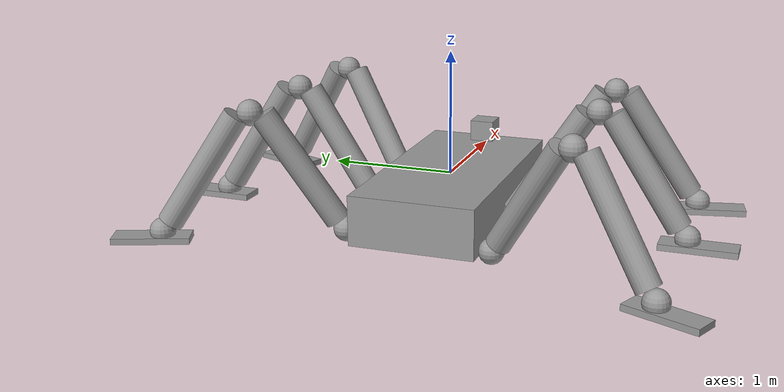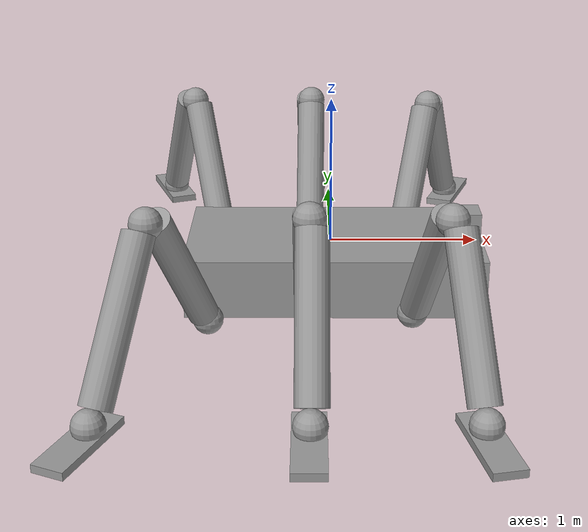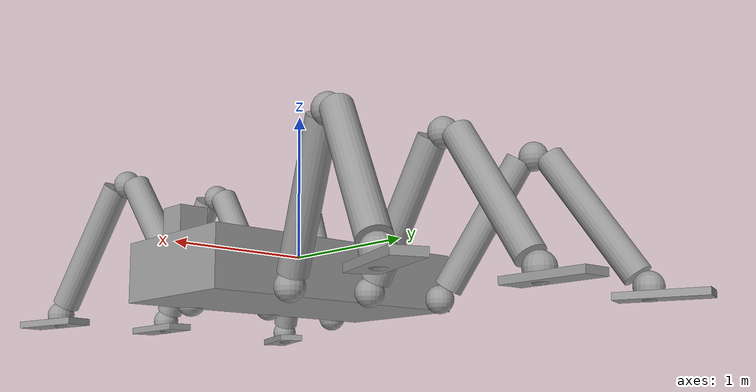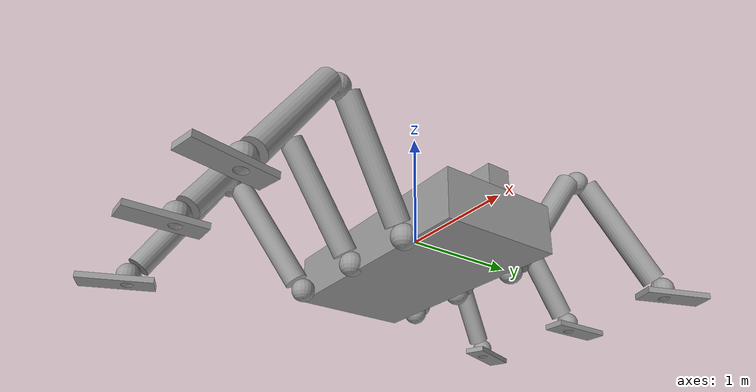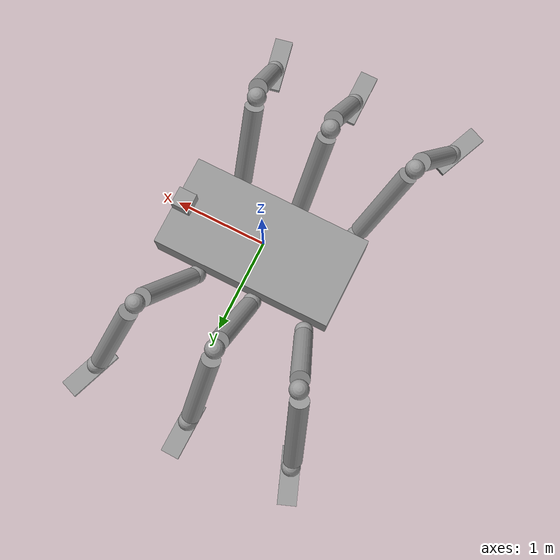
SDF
<?xml version='1.0'?>
<sdf version='1.6'>
  <model name='fixed_spider'>
    <link name='link_0'>
      <pose frame=''>0.026826 -0.008479 -0.14871 0 -0 0</pose>
      <inertial>
        <mass>1</mass>
        <inertia>
          <ixx>0.166667</ixx>
          <ixy>0</ixy>
          <ixz>0</ixz>
          <iyy>0.166667</iyy>
          <iyz>0</iyz>
          <izz>0.166667</izz>
        </inertia>
        <pose frame=''>0 0 0 0 -0 0</pose>
      </inertial>
      <gravity>1</gravity>
      <self_collide>0</self_collide>
      <kinematic>0</kinematic>
      <visual name='visual'>
        <pose frame=''>0 0 0 0 -0 0</pose>
        <geometry>
          <box>
            <size>2 1 0.4</size>
          </box>
        </geometry>
        <material>
          <lighting>1</lighting>
          <script>
            <uri>file://media/materials/scripts/gazebo.material</uri>
            <name>Gazebo/Grey</name>
          </script>
          <ambient>0.3 0.3 0.3 1</ambient>
          <diffuse>0.7 0.7 0.7 1</diffuse>
          <specular>0.01 0.01 0.01 1</specular>
          <emissive>0 0 0 1</emissive>
          <shader type='vertex'>
            <normal_map>__default__</normal_map>
          </shader>
        </material>
        <cast_shadows>1</cast_shadows>
        <transparency>0</transparency>
      </visual>
      <collision name='collision'>
        <laser_retro>0</laser_retro>
        <max_contacts>10</max_contacts>
        <pose frame=''>0 0 0 0 -0 0</pose>
        <geometry>
          <box>
            <size>2 1 0.4</size>
          </box>
        </geometry>
        <surface>
          <friction>
            <ode>
              <mu>1</mu>
              <mu2>1</mu2>
              <fdir1>0 0 0</fdir1>
              <slip1>0</slip1>
              <slip2>0</slip2>
            </ode>
            <torsional>
              <coefficient>1</coefficient>
              <patch_radius>0</patch_radius>
              <surface_radius>0</surface_radius>
              <use_patch_radius>1</use_patch_radius>
              <ode>
                <slip>0</slip>
              </ode>
            </torsional>
          </friction>
          <bounce>
            <restitution_coefficient>0</restitution_coefficient>
            <threshold>1e+06</threshold>
          </bounce>
          <contact>
            <collide_without_contact>0</collide_without_contact>
            <collide_without_contact_bitmask>1</collide_without_contact_bitmask>
            <collide_bitmask>1</collide_bitmask>
            <ode>
              <soft_cfm>0</soft_cfm>
              <soft_erp>0.2</soft_erp>
              <kp>1e+13</kp>
              <kd>1</kd>
              <max_vel>0.01</max_vel>
              <min_depth>0</min_depth>
            </ode>
            <bullet>
              <split_impulse>1</split_impulse>
              <split_impulse_penetration_threshold>-0.01</split_impulse_penetration_threshold>
              <soft_cfm>0</soft_cfm>
              <soft_erp>0.2</soft_erp>
              <kp>1e+13</kp>
              <kd>1</kd>
            </bullet>
          </contact>
        </surface>
      </collision>
    </link>
    <link name='link_1'>
      <pose frame=''>0.921363 -0.008479 0.124747 0 -0 0</pose>
      <inertial>
        <mass>1</mass>
        <inertia>
          <ixx>0.166667</ixx>
          <ixy>0</ixy>
          <ixz>0</ixz>
          <iyy>0.166667</iyy>
          <iyz>0</iyz>
          <izz>0.166667</izz>
        </inertia>
        <pose frame=''>0 0 0 0 -0 0</pose>
      </inertial>
      <gravity>1</gravity>
      <self_collide>0</self_collide>
      <kinematic>0</kinematic>
      <visual name='visual'>
        <pose frame=''>0 0 0 0 -0 0</pose>
        <geometry>
          <box>
            <size>0.2 0.2 0.2</size>
          </box>
        </geometry>
        <material>
          <lighting>1</lighting>
          <script>
            <uri>file://media/materials/scripts/gazebo.material</uri>
            <name>Gazebo/Grey</name>
          </script>
          <ambient>0.3 0.3 0.3 1</ambient>
          <diffuse>0.7 0.7 0.7 1</diffuse>
          <specular>0.01 0.01 0.01 1</specular>
          <emissive>0 0 0 1</emissive>
          <shader type='vertex'>
            <normal_map>__default__</normal_map>
          </shader>
        </material>
        <cast_shadows>1</cast_shadows>
        <transparency>0</transparency>
      </visual>
      <collision name='collision'>
        <laser_retro>0</laser_retro>
        <max_contacts>10</max_contacts>
        <pose frame=''>0 0 0 0 -0 0</pose>
        <geometry>
          <box>
            <size>0.2 0.2 0.2</size>
          </box>
        </geometry>
        <surface>
          <friction>
            <ode>
              <mu>1</mu>
              <mu2>1</mu2>
              <fdir1>0 0 0</fdir1>
              <slip1>0</slip1>
              <slip2>0</slip2>
            </ode>
            <torsional>
              <coefficient>1</coefficient>
              <patch_radius>0</patch_radius>
              <surface_radius>0</surface_radius>
              <use_patch_radius>1</use_patch_radius>
              <ode>
                <slip>0</slip>
              </ode>
            </torsional>
          </friction>
          <bounce>
            <restitution_coefficient>0</restitution_coefficient>
            <threshold>1e+06</threshold>
          </bounce>
          <contact>
            <collide_without_contact>0</collide_without_contact>
            <collide_without_contact_bitmask>1</collide_without_contact_bitmask>
            <collide_bitmask>1</collide_bitmask>
            <ode>
              <soft_cfm>0</soft_cfm>
              <soft_erp>0.2</soft_erp>
              <kp>1e+13</kp>
              <kd>1</kd>
              <max_vel>0.01</max_vel>
              <min_depth>0</min_depth>
            </ode>
            <bullet>
              <split_impulse>1</split_impulse>
              <split_impulse_penetration_threshold>-0.01</split_impulse_penetration_threshold>
              <soft_cfm>0</soft_cfm>
              <soft_erp>0.2</soft_erp>
              <kp>1e+13</kp>
              <kd>1</kd>
            </bullet>
          </contact>
        </surface>
      </collision>
    </link>
    <model name='leg'>
      <link name='link_1'>
        <pose frame=''>-0.170373 0.465226 0.194106 0 -0 0</pose>
        <inertial>
          <mass>1</mass>
          <inertia>
            <ixx>0.145833</ixx>
            <ixy>0</ixy>
            <ixz>0</ixz>
            <iyy>0.145833</iyy>
            <iyz>0</iyz>
            <izz>0.125</izz>
          </inertia>
          <pose frame=''>0 0 0 0 -0 0</pose>
        </inertial>
        <gravity>1</gravity>
        <self_collide>0</self_collide>
        <kinematic>0</kinematic>
        <visual name='visual'>
          <pose frame=''>0 0 0 -2.56637 0 0</pose>
          <geometry>
            <cylinder>
              <radius>0.1</radius>
              <length>1</length>
            </cylinder>
          </geometry>
          <material>
            <lighting>1</lighting>
            <script>
              <uri>file://media/materials/scripts/gazebo.material</uri>
              <name>Gazebo/Grey</name>
            </script>
            <ambient>0.3 0.3 0.3 1</ambient>
            <diffuse>0.7 0.7 0.7 1</diffuse>
            <specular>0.01 0.01 0.01 1</specular>
            <emissive>0 0 0 1</emissive>
            <shader type='vertex'>
              <normal_map>__default__</normal_map>
            </shader>
          </material>
          <cast_shadows>1</cast_shadows>
          <transparency>0</transparency>
        </visual>
        <collision name='collision'>
          <laser_retro>0</laser_retro>
          <max_contacts>10</max_contacts>
          <pose frame=''>0 0 0 -2.56637 0 0</pose>
          <geometry>
            <cylinder>
              <radius>0.1</radius>
              <length>1</length>
            </cylinder>
          </geometry>
          <surface>
            <friction>
              <ode>
                <mu>1</mu>
                <mu2>1</mu2>
                <fdir1>0 0 0</fdir1>
                <slip1>0</slip1>
                <slip2>0</slip2>
              </ode>
              <torsional>
                <coefficient>1</coefficient>
                <patch_radius>0</patch_radius>
                <surface_radius>0</surface_radius>
                <use_patch_radius>1</use_patch_radius>
                <ode>
                  <slip>0</slip>
                </ode>
              </torsional>
            </friction>
            <bounce>
              <restitution_coefficient>0</restitution_coefficient>
              <threshold>1e+06</threshold>
            </bounce>
            <contact>
              <collide_without_contact>0</collide_without_contact>
              <collide_without_contact_bitmask>1</collide_without_contact_bitmask>
              <collide_bitmask>1</collide_bitmask>
              <ode>
                <soft_cfm>0</soft_cfm>
                <soft_erp>0.2</soft_erp>
                <kp>1e+13</kp>
                <kd>1</kd>
                <max_vel>0.01</max_vel>
                <min_depth>0</min_depth>
              </ode>
              <bullet>
                <split_impulse>1</split_impulse>
                <split_impulse_penetration_threshold>-0.01</split_impulse_penetration_threshold>
                <soft_cfm>0</soft_cfm>
                <soft_erp>0.2</soft_erp>
                <kp>1e+13</kp>
                <kd>1</kd>
              </bullet>
            </contact>
          </surface>
        </collision>
      </link>
      <link name='link_1_clone'>
        <pose frame=''>-0.155317 -0.274157 0.194106 0 -0 0</pose>
        <inertial>
          <mass>1</mass>
          <inertia>
            <ixx>0.145833</ixx>
            <ixy>0</ixy>
            <ixz>0</ixz>
            <iyy>0.145833</iyy>
            <iyz>0</iyz>
            <izz>0.125</izz>
          </inertia>
          <pose frame=''>0 0 0 0 -0 0</pose>
        </inertial>
        <self_collide>0</self_collide>
        <kinematic>0</kinematic>
        <gravity>1</gravity>
        <visual name='visual'>
          <pose frame=''>0 0 0 2.56637 -0 0</pose>
          <geometry>
            <cylinder>
              <radius>0.1</radius>
              <length>1</length>
            </cylinder>
          </geometry>
          <material>
            <lighting>1</lighting>
            <script>
              <uri>file://media/materials/scripts/gazebo.material</uri>
              <name>Gazebo/Grey</name>
            </script>
            <ambient>0.3 0.3 0.3 1</ambient>
            <diffuse>0.7 0.7 0.7 1</diffuse>
            <specular>0.01 0.01 0.01 1</specular>
            <emissive>0 0 0 1</emissive>
            <shader type='vertex'>
              <normal_map>__default__</normal_map>
            </shader>
          </material>
          <cast_shadows>1</cast_shadows>
          <transparency>0</transparency>
        </visual>
        <collision name='collision'>
          <laser_retro>0</laser_retro>
          <max_contacts>10</max_contacts>
          <pose frame=''>0 0 0 2.56637 -0 0</pose>
          <geometry>
            <cylinder>
              <radius>0.1</radius>
              <length>1</length>
            </cylinder>
          </geometry>
          <surface>
            <friction>
              <ode>
                <mu>1</mu>
                <mu2>1</mu2>
                <fdir1>0 0 0</fdir1>
                <slip1>0</slip1>
                <slip2>0</slip2>
              </ode>
              <torsional>
                <coefficient>1</coefficient>
                <patch_radius>0</patch_radius>
                <surface_radius>0</surface_radius>
                <use_patch_radius>1</use_patch_radius>
                <ode>
                  <slip>0</slip>
                </ode>
              </torsional>
            </friction>
            <bounce>
              <restitution_coefficient>0</restitution_coefficient>
              <threshold>1e+06</threshold>
            </bounce>
            <contact>
              <collide_without_contact>0</collide_without_contact>
              <collide_without_contact_bitmask>1</collide_without_contact_bitmask>
              <collide_bitmask>1</collide_bitmask>
              <ode>
                <soft_cfm>0</soft_cfm>
                <soft_erp>0.2</soft_erp>
                <kp>1e+13</kp>
                <kd>1</kd>
                <max_vel>0.01</max_vel>
                <min_depth>0</min_depth>
              </ode>
              <bullet>
                <split_impulse>1</split_impulse>
                <split_impulse_penetration_threshold>-0.01</split_impulse_penetration_threshold>
                <soft_cfm>0</soft_cfm>
                <soft_erp>0.2</soft_erp>
                <kp>1e+13</kp>
                <kd>1</kd>
              </bullet>
            </contact>
          </surface>
        </collision>
      </link>
      <link name='link_2'>
        <pose frame=''>-0.169792 0.099257 0.628941 0 -0 0</pose>
        <inertial>
          <mass>1</mass>
          <inertia>
            <ixx>0.1</ixx>
            <ixy>0</ixy>
            <ixz>0</ixz>
            <iyy>0.1</iyy>
            <iyz>0</iyz>
            <izz>0.1</izz>
          </inertia>
          <pose frame=''>0 0 0 0 -0 0</pose>
        </inertial>
        <gravity>1</gravity>
        <self_collide>0</self_collide>
        <kinematic>0</kinematic>
        <visual name='visual'>
          <pose frame=''>0 0 0 0 -0 0</pose>
          <geometry>
            <sphere>
              <radius>0.1</radius>
            </sphere>
          </geometry>
          <material>
            <lighting>1</lighting>
            <script>
              <uri>file://media/materials/scripts/gazebo.material</uri>
              <name>Gazebo/Grey</name>
            </script>
            <ambient>0.3 0.3 0.3 1</ambient>
            <diffuse>0.7 0.7 0.7 1</diffuse>
            <specular>0.01 0.01 0.01 1</specular>
            <emissive>0 0 0 1</emissive>
            <shader type='vertex'>
              <normal_map>__default__</normal_map>
            </shader>
          </material>
          <cast_shadows>1</cast_shadows>
          <transparency>0</transparency>
        </visual>
        <collision name='collision'>
          <laser_retro>0</laser_retro>
          <max_contacts>10</max_contacts>
          <pose frame=''>0 0 0 0 -0 0</pose>
          <geometry>
            <sphere>
              <radius>0.1</radius>
            </sphere>
          </geometry>
          <surface>
            <friction>
              <ode>
                <mu>1</mu>
                <mu2>1</mu2>
                <fdir1>0 0 0</fdir1>
                <slip1>0</slip1>
                <slip2>0</slip2>
              </ode>
              <torsional>
                <coefficient>1</coefficient>
                <patch_radius>0</patch_radius>
                <surface_radius>0</surface_radius>
                <use_patch_radius>1</use_patch_radius>
                <ode>
                  <slip>0</slip>
                </ode>
              </torsional>
            </friction>
            <bounce>
              <restitution_coefficient>0</restitution_coefficient>
              <threshold>1e+06</threshold>
            </bounce>
            <contact>
              <collide_without_contact>0</collide_without_contact>
              <collide_without_contact_bitmask>1</collide_without_contact_bitmask>
              <collide_bitmask>1</collide_bitmask>
              <ode>
                <soft_cfm>0</soft_cfm>
                <soft_erp>0.2</soft_erp>
                <kp>1e+13</kp>
                <kd>1</kd>
                <max_vel>0.01</max_vel>
                <min_depth>0</min_depth>
              </ode>
              <bullet>
                <split_impulse>1</split_impulse>
                <split_impulse_penetration_threshold>-0.01</split_impulse_penetration_threshold>
                <soft_cfm>0</soft_cfm>
                <soft_erp>0.2</soft_erp>
                <kp>1e+13</kp>
                <kd>1</kd>
              </bullet>
            </contact>
          </surface>
        </collision>
      </link>
      <link name='link_2_clone'>
        <pose frame=''>-0.163772 -0.612033 -0.298449 0 -0 0</pose>
        <inertial>
          <mass>1</mass>
          <inertia>
            <ixx>0.1</ixx>
            <ixy>0</ixy>
            <ixz>0</ixz>
            <iyy>0.1</iyy>
            <iyz>0</iyz>
            <izz>0.1</izz>
          </inertia>
          <pose frame=''>0 0 0 0 -0 0</pose>
        </inertial>
        <self_collide>0</self_collide>
        <kinematic>0</kinematic>
        <visual name='visual'>
          <pose frame=''>0 0 0 0 -0 0</pose>
          <geometry>
            <sphere>
              <radius>0.1</radius>
            </sphere>
          </geometry>
          <material>
            <lighting>1</lighting>
            <script>
              <uri>file://media/materials/scripts/gazebo.material</uri>
              <name>Gazebo/Grey</name>
            </script>
            <ambient>0.3 0.3 0.3 1</ambient>
            <diffuse>0.7 0.7 0.7 1</diffuse>
            <specular>0.01 0.01 0.01 1</specular>
            <emissive>0 0 0 1</emissive>
            <shader type='vertex'>
              <normal_map>__default__</normal_map>
            </shader>
          </material>
          <cast_shadows>1</cast_shadows>
          <transparency>0</transparency>
        </visual>
        <collision name='collision'>
          <laser_retro>0</laser_retro>
          <max_contacts>10</max_contacts>
          <pose frame=''>0 0 0 0 -0 0</pose>
          <geometry>
            <sphere>
              <radius>0.1</radius>
            </sphere>
          </geometry>
          <surface>
            <friction>
              <ode>
                <mu>1</mu>
                <mu2>1</mu2>
                <fdir1>0 0 0</fdir1>
                <slip1>0</slip1>
                <slip2>0</slip2>
              </ode>
              <torsional>
                <coefficient>1</coefficient>
                <patch_radius>0</patch_radius>
                <surface_radius>0</surface_radius>
                <use_patch_radius>1</use_patch_radius>
                <ode>
                  <slip>0</slip>
                </ode>
              </torsional>
            </friction>
            <bounce>
              <restitution_coefficient>0</restitution_coefficient>
              <threshold>1e+06</threshold>
            </bounce>
            <contact>
              <collide_without_contact>0</collide_without_contact>
              <collide_without_contact_bitmask>1</collide_without_contact_bitmask>
              <collide_bitmask>1</collide_bitmask>
              <ode>
                <soft_cfm>0</soft_cfm>
                <soft_erp>0.2</soft_erp>
                <kp>1e+13</kp>
                <kd>1</kd>
                <max_vel>0.01</max_vel>
                <min_depth>0</min_depth>
              </ode>
              <bullet>
                <split_impulse>1</split_impulse>
                <split_impulse_penetration_threshold>-0.01</split_impulse_penetration_threshold>
                <soft_cfm>0</soft_cfm>
                <soft_erp>0.2</soft_erp>
                <kp>1e+13</kp>
                <kd>1</kd>
              </bullet>
            </contact>
          </surface>
        </collision>
      </link>
      <link name='link_3'>
        <pose frame=''>-0.170373 -0.699304 -0.359352 0 -0 0</pose>
        <inertial>
          <mass>1</mass>
          <inertia>
            <ixx>0.166667</ixx>
            <ixy>0</ixy>
            <ixz>0</ixz>
            <iyy>0.166667</iyy>
            <iyz>0</iyz>
            <izz>0.166667</izz>
          </inertia>
          <pose frame=''>0 0 0 0 -0 0</pose>
        </inertial>
        <gravity>1</gravity>
        <self_collide>0</self_collide>
        <kinematic>0</kinematic>
        <visual name='visual'>
          <pose frame=''>0 0 0 0 -0 0</pose>
          <geometry>
            <box>
              <size>0.2 0.6 0.05</size>
            </box>
          </geometry>
          <material>
            <lighting>1</lighting>
            <script>
              <uri>file://media/materials/scripts/gazebo.material</uri>
              <name>Gazebo/Grey</name>
            </script>
            <ambient>0.3 0.3 0.3 1</ambient>
            <diffuse>0.7 0.7 0.7 1</diffuse>
            <specular>0.01 0.01 0.01 1</specular>
            <emissive>0 0 0 1</emissive>
            <shader type='vertex'>
              <normal_map>__default__</normal_map>
            </shader>
          </material>
          <cast_shadows>1</cast_shadows>
          <transparency>0</transparency>
        </visual>
        <collision name='collision'>
          <laser_retro>0</laser_retro>
          <max_contacts>10</max_contacts>
          <pose frame=''>0 0 0 0 -0 0</pose>
          <geometry>
            <box>
              <size>0.2 0.6 0.05</size>
            </box>
          </geometry>
          <surface>
            <friction>
              <ode>
                <mu>1</mu>
                <mu2>1</mu2>
                <fdir1>0 0 0</fdir1>
                <slip1>0</slip1>
                <slip2>0</slip2>
              </ode>
              <torsional>
                <coefficient>1</coefficient>
                <patch_radius>0</patch_radius>
                <surface_radius>0</surface_radius>
                <use_patch_radius>1</use_patch_radius>
                <ode>
                  <slip>0</slip>
                </ode>
              </torsional>
            </friction>
            <bounce>
              <restitution_coefficient>0</restitution_coefficient>
              <threshold>1e+06</threshold>
            </bounce>
            <contact>
              <collide_without_contact>0</collide_without_contact>
              <collide_without_contact_bitmask>1</collide_without_contact_bitmask>
              <collide_bitmask>1</collide_bitmask>
              <ode>
                <soft_cfm>0</soft_cfm>
                <soft_erp>0.2</soft_erp>
                <kp>1e+13</kp>
                <kd>1</kd>
                <max_vel>0.01</max_vel>
                <min_depth>0</min_depth>
              </ode>
              <bullet>
                <split_impulse>1</split_impulse>
                <split_impulse_penetration_threshold>-0.01</split_impulse_penetration_threshold>
                <soft_cfm>0</soft_cfm>
                <soft_erp>0.2</soft_erp>
                <kp>1e+13</kp>
                <kd>1</kd>
              </bullet>
            </contact>
          </surface>
        </collision>
      </link>
      <link name='link_11'>
        <pose frame=''>-0.17 0.8 -0.3 0 -0 0</pose>
        <inertial>
          <mass>1</mass>
          <inertia>
            <ixx>0.1</ixx>
            <ixy>0</ixy>
            <ixz>0</ixz>
            <iyy>0.1</iyy>
            <iyz>0</iyz>
            <izz>0.1</izz>
          </inertia>
          <pose frame=''>0 0 0 0 -0 0</pose>
        </inertial>
        <gravity>1</gravity>
        <self_collide>0</self_collide>
        <kinematic>0</kinematic>
        <visual name='visual'>
          <pose frame=''>0 0 0 0 -0 0</pose>
          <geometry>
            <sphere>
              <radius>0.1</radius>
            </sphere>
          </geometry>
          <material>
            <lighting>1</lighting>
            <script>
              <uri>file://media/materials/scripts/gazebo.material</uri>
              <name>Gazebo/Grey</name>
            </script>
            <ambient>0.3 0.3 0.3 1</ambient>
            <diffuse>0.7 0.7 0.7 1</diffuse>
            <specular>0.01 0.01 0.01 1</specular>
            <emissive>0 0 0 1</emissive>
            <shader type='vertex'>
              <normal_map>__default__</normal_map>
            </shader>
          </material>
          <cast_shadows>1</cast_shadows>
          <transparency>0</transparency>
        </visual>
        <collision name='collision'>
          <laser_retro>0</laser_retro>
          <max_contacts>10</max_contacts>
          <pose frame=''>0 0 0 0 -0 0</pose>
          <geometry>
            <sphere>
              <radius>0.1</radius>
            </sphere>
          </geometry>
          <surface>
            <friction>
              <ode>
                <mu>1</mu>
                <mu2>1</mu2>
                <fdir1>0 0 0</fdir1>
                <slip1>0</slip1>
                <slip2>0</slip2>
              </ode>
              <torsional>
                <coefficient>1</coefficient>
                <patch_radius>0</patch_radius>
                <surface_radius>0</surface_radius>
                <use_patch_radius>1</use_patch_radius>
                <ode>
                  <slip>0</slip>
                </ode>
              </torsional>
            </friction>
            <bounce>
              <restitution_coefficient>0</restitution_coefficient>
              <threshold>1e+06</threshold>
            </bounce>
            <contact>
              <collide_without_contact>0</collide_without_contact>
              <collide_without_contact_bitmask>1</collide_without_contact_bitmask>
              <collide_bitmask>1</collide_bitmask>
              <ode>
                <soft_cfm>0</soft_cfm>
                <soft_erp>0.2</soft_erp>
                <kp>1e+13</kp>
                <kd>1</kd>
                <max_vel>0.01</max_vel>
                <min_depth>0</min_depth>
              </ode>
              <bullet>
                <split_impulse>1</split_impulse>
                <split_impulse_penetration_threshold>-0.01</split_impulse_penetration_threshold>
                <soft_cfm>0</soft_cfm>
                <soft_erp>0.2</soft_erp>
                <kp>1e+13</kp>
                <kd>1</kd>
              </bullet>
            </contact>
          </surface>
        </collision>
      </link>
      <joint name='link_1_JOINT_0' type='fixed'>
        <parent>link_1</parent>
        <child>link_2</child>
        <pose frame=''>0 0 0 0 -0 0</pose>
        <physics>
          <ode>
            <limit>
              <cfm>0</cfm>
              <erp>0.2</erp>
            </limit>
            <suspension>
              <cfm>0</cfm>
              <erp>0.2</erp>
            </suspension>
          </ode>
        </physics>
      </joint>
      <joint name='link_1_clone_JOINT_2' type='ball'>
        <parent>link_1_clone</parent>
        <child>link_2_clone</child>
        <pose frame=''>0 0 0 0 -0 0</pose>
        <physics>
          <ode>
            <limit>
              <cfm>0</cfm>
              <erp>0.2</erp>
            </limit>
            <suspension>
              <cfm>0</cfm>
              <erp>0.2</erp>
            </suspension>
          </ode>
        </physics>
      </joint>
      <joint name='link_2_JOINT_1' type='fixed'>
        <parent>link_2</parent>
        <child>link_1_clone</child>
        <pose frame=''>0 0 0 0 -0 0</pose>
        <physics>
          <ode>
            <limit>
              <cfm>0</cfm>
              <erp>0.2</erp>
            </limit>
            <suspension>
              <cfm>0</cfm>
              <erp>0.2</erp>
            </suspension>
          </ode>
        </physics>
      </joint>
      <joint name='link_2_clone_JOINT_3' type='ball'>
        <parent>link_1_clone</parent>
        <child>link_3</child>
        <pose frame=''>0 0 0 0 -0 0</pose>
        <physics>
          <ode>
            <limit>
              <cfm>0</cfm>
              <erp>0.2</erp>
            </limit>
            <suspension>
              <cfm>0</cfm>
              <erp>0.2</erp>
            </suspension>
          </ode>
        </physics>
      </joint>
      <joint name='link_11_JOINT_3' type='fixed'>
        <parent>link_11</parent>
        <child>link_1</child>
        <pose frame=''>0 0 0 0 -0 0</pose>
        <physics>
          <ode>
            <limit>
              <cfm>0</cfm>
              <erp>0.2</erp>
            </limit>
            <suspension>
              <cfm>0</cfm>
              <erp>0.2</erp>
            </suspension>
          </ode>
        </physics>
      </joint>
      <static>0</static>
      <allow_auto_disable>1</allow_auto_disable>
      <pose frame=''>-0.961822 -1.39637 -0.014706 0 0 -0.402063</pose>
    </model>
    <model name='leg_0'>
      <link name='link_1'>
        <pose frame=''>-0.170373 0.465226 0.194106 0 -0 0</pose>
        <inertial>
          <mass>1</mass>
          <inertia>
            <ixx>0.145833</ixx>
            <ixy>0</ixy>
            <ixz>0</ixz>
            <iyy>0.145833</iyy>
            <iyz>0</iyz>
            <izz>0.125</izz>
          </inertia>
          <pose frame=''>0 0 0 0 -0 0</pose>
        </inertial>
        <gravity>1</gravity>
        <self_collide>0</self_collide>
        <kinematic>0</kinematic>
        <visual name='visual'>
          <pose frame=''>0 0 0 -2.56637 0 0</pose>
          <geometry>
            <cylinder>
              <radius>0.1</radius>
              <length>1</length>
            </cylinder>
          </geometry>
          <material>
            <lighting>1</lighting>
            <script>
              <uri>file://media/materials/scripts/gazebo.material</uri>
              <name>Gazebo/Grey</name>
            </script>
            <ambient>0.3 0.3 0.3 1</ambient>
            <diffuse>0.7 0.7 0.7 1</diffuse>
            <specular>0.01 0.01 0.01 1</specular>
            <emissive>0 0 0 1</emissive>
            <shader type='vertex'>
              <normal_map>__default__</normal_map>
            </shader>
          </material>
          <cast_shadows>1</cast_shadows>
          <transparency>0</transparency>
        </visual>
        <collision name='collision'>
          <laser_retro>0</laser_retro>
          <max_contacts>10</max_contacts>
          <pose frame=''>0 0 0 -2.56637 0 0</pose>
          <geometry>
            <cylinder>
              <radius>0.1</radius>
              <length>1</length>
            </cylinder>
          </geometry>
          <surface>
            <friction>
              <ode>
                <mu>1</mu>
                <mu2>1</mu2>
                <fdir1>0 0 0</fdir1>
                <slip1>0</slip1>
                <slip2>0</slip2>
              </ode>
              <torsional>
                <coefficient>1</coefficient>
                <patch_radius>0</patch_radius>
                <surface_radius>0</surface_radius>
                <use_patch_radius>1</use_patch_radius>
                <ode>
                  <slip>0</slip>
                </ode>
              </torsional>
            </friction>
            <bounce>
              <restitution_coefficient>0</restitution_coefficient>
              <threshold>1e+06</threshold>
            </bounce>
            <contact>
              <collide_without_contact>0</collide_without_contact>
              <collide_without_contact_bitmask>1</collide_without_contact_bitmask>
              <collide_bitmask>1</collide_bitmask>
              <ode>
                <soft_cfm>0</soft_cfm>
                <soft_erp>0.2</soft_erp>
                <kp>1e+13</kp>
                <kd>1</kd>
                <max_vel>0.01</max_vel>
                <min_depth>0</min_depth>
              </ode>
              <bullet>
                <split_impulse>1</split_impulse>
                <split_impulse_penetration_threshold>-0.01</split_impulse_penetration_threshold>
                <soft_cfm>0</soft_cfm>
                <soft_erp>0.2</soft_erp>
                <kp>1e+13</kp>
                <kd>1</kd>
              </bullet>
            </contact>
          </surface>
        </collision>
      </link>
      <link name='link_1_clone'>
        <pose frame=''>-0.155317 -0.274157 0.194106 0 -0 0</pose>
        <inertial>
          <mass>1</mass>
          <inertia>
            <ixx>0.145833</ixx>
            <ixy>0</ixy>
            <ixz>0</ixz>
            <iyy>0.145833</iyy>
            <iyz>0</iyz>
            <izz>0.125</izz>
          </inertia>
          <pose frame=''>0 0 0 0 -0 0</pose>
        </inertial>
        <self_collide>0</self_collide>
        <kinematic>0</kinematic>
        <gravity>1</gravity>
        <visual name='visual'>
          <pose frame=''>0 0 0 2.56637 -0 0</pose>
          <geometry>
            <cylinder>
              <radius>0.1</radius>
              <length>1</length>
            </cylinder>
          </geometry>
          <material>
            <lighting>1</lighting>
            <script>
              <uri>file://media/materials/scripts/gazebo.material</uri>
              <name>Gazebo/Grey</name>
            </script>
            <ambient>0.3 0.3 0.3 1</ambient>
            <diffuse>0.7 0.7 0.7 1</diffuse>
            <specular>0.01 0.01 0.01 1</specular>
            <emissive>0 0 0 1</emissive>
            <shader type='vertex'>
              <normal_map>__default__</normal_map>
            </shader>
          </material>
          <cast_shadows>1</cast_shadows>
          <transparency>0</transparency>
        </visual>
        <collision name='collision'>
          <laser_retro>0</laser_retro>
          <max_contacts>10</max_contacts>
          <pose frame=''>0 0 0 2.56637 -0 0</pose>
          <geometry>
            <cylinder>
              <radius>0.1</radius>
              <length>1</length>
            </cylinder>
          </geometry>
          <surface>
            <friction>
              <ode>
                <mu>1</mu>
                <mu2>1</mu2>
                <fdir1>0 0 0</fdir1>
                <slip1>0</slip1>
                <slip2>0</slip2>
              </ode>
              <torsional>
                <coefficient>1</coefficient>
                <patch_radius>0</patch_radius>
                <surface_radius>0</surface_radius>
                <use_patch_radius>1</use_patch_radius>
                <ode>
                  <slip>0</slip>
                </ode>
              </torsional>
            </friction>
            <bounce>
              <restitution_coefficient>0</restitution_coefficient>
              <threshold>1e+06</threshold>
            </bounce>
            <contact>
              <collide_without_contact>0</collide_without_contact>
              <collide_without_contact_bitmask>1</collide_without_contact_bitmask>
              <collide_bitmask>1</collide_bitmask>
              <ode>
                <soft_cfm>0</soft_cfm>
                <soft_erp>0.2</soft_erp>
                <kp>1e+13</kp>
                <kd>1</kd>
                <max_vel>0.01</max_vel>
                <min_depth>0</min_depth>
              </ode>
              <bullet>
                <split_impulse>1</split_impulse>
                <split_impulse_penetration_threshold>-0.01</split_impulse_penetration_threshold>
                <soft_cfm>0</soft_cfm>
                <soft_erp>0.2</soft_erp>
                <kp>1e+13</kp>
                <kd>1</kd>
              </bullet>
            </contact>
          </surface>
        </collision>
      </link>
      <link name='link_2'>
        <pose frame=''>-0.169792 0.099257 0.628941 0 -0 0</pose>
        <inertial>
          <mass>1</mass>
          <inertia>
            <ixx>0.1</ixx>
            <ixy>0</ixy>
            <ixz>0</ixz>
            <iyy>0.1</iyy>
            <iyz>0</iyz>
            <izz>0.1</izz>
          </inertia>
          <pose frame=''>0 0 0 0 -0 0</pose>
        </inertial>
        <gravity>1</gravity>
        <self_collide>0</self_collide>
        <kinematic>0</kinematic>
        <visual name='visual'>
          <pose frame=''>0 0 0 0 -0 0</pose>
          <geometry>
            <sphere>
              <radius>0.1</radius>
            </sphere>
          </geometry>
          <material>
            <lighting>1</lighting>
            <script>
              <uri>file://media/materials/scripts/gazebo.material</uri>
              <name>Gazebo/Grey</name>
            </script>
            <ambient>0.3 0.3 0.3 1</ambient>
            <diffuse>0.7 0.7 0.7 1</diffuse>
            <specular>0.01 0.01 0.01 1</specular>
            <emissive>0 0 0 1</emissive>
            <shader type='vertex'>
              <normal_map>__default__</normal_map>
            </shader>
          </material>
          <cast_shadows>1</cast_shadows>
          <transparency>0</transparency>
        </visual>
        <collision name='collision'>
          <laser_retro>0</laser_retro>
          <max_contacts>10</max_contacts>
          <pose frame=''>0 0 0 0 -0 0</pose>
          <geometry>
            <sphere>
              <radius>0.1</radius>
            </sphere>
          </geometry>
          <surface>
            <friction>
              <ode>
                <mu>1</mu>
                <mu2>1</mu2>
                <fdir1>0 0 0</fdir1>
                <slip1>0</slip1>
                <slip2>0</slip2>
              </ode>
              <torsional>
                <coefficient>1</coefficient>
                <patch_radius>0</patch_radius>
                <surface_radius>0</surface_radius>
                <use_patch_radius>1</use_patch_radius>
                <ode>
                  <slip>0</slip>
                </ode>
              </torsional>
            </friction>
            <bounce>
              <restitution_coefficient>0</restitution_coefficient>
              <threshold>1e+06</threshold>
            </bounce>
            <contact>
              <collide_without_contact>0</collide_without_contact>
              <collide_without_contact_bitmask>1</collide_without_contact_bitmask>
              <collide_bitmask>1</collide_bitmask>
              <ode>
                <soft_cfm>0</soft_cfm>
                <soft_erp>0.2</soft_erp>
                <kp>1e+13</kp>
                <kd>1</kd>
                <max_vel>0.01</max_vel>
                <min_depth>0</min_depth>
              </ode>
              <bullet>
                <split_impulse>1</split_impulse>
                <split_impulse_penetration_threshold>-0.01</split_impulse_penetration_threshold>
                <soft_cfm>0</soft_cfm>
                <soft_erp>0.2</soft_erp>
                <kp>1e+13</kp>
                <kd>1</kd>
              </bullet>
            </contact>
          </surface>
        </collision>
      </link>
      <link name='link_2_clone'>
        <pose frame=''>-0.163772 -0.612033 -0.298449 0 -0 0</pose>
        <inertial>
          <mass>1</mass>
          <inertia>
            <ixx>0.1</ixx>
            <ixy>0</ixy>
            <ixz>0</ixz>
            <iyy>0.1</iyy>
            <iyz>0</iyz>
            <izz>0.1</izz>
          </inertia>
          <pose frame=''>0 0 0 0 -0 0</pose>
        </inertial>
        <self_collide>0</self_collide>
        <kinematic>0</kinematic>
        <visual name='visual'>
          <pose frame=''>0 0 0 0 -0 0</pose>
          <geometry>
            <sphere>
              <radius>0.1</radius>
            </sphere>
          </geometry>
          <material>
            <lighting>1</lighting>
            <script>
              <uri>file://media/materials/scripts/gazebo.material</uri>
              <name>Gazebo/Grey</name>
            </script>
            <ambient>0.3 0.3 0.3 1</ambient>
            <diffuse>0.7 0.7 0.7 1</diffuse>
            <specular>0.01 0.01 0.01 1</specular>
            <emissive>0 0 0 1</emissive>
            <shader type='vertex'>
              <normal_map>__default__</normal_map>
            </shader>
          </material>
          <cast_shadows>1</cast_shadows>
          <transparency>0</transparency>
        </visual>
        <collision name='collision'>
          <laser_retro>0</laser_retro>
          <max_contacts>10</max_contacts>
          <pose frame=''>0 0 0 0 -0 0</pose>
          <geometry>
            <sphere>
              <radius>0.1</radius>
            </sphere>
          </geometry>
          <surface>
            <friction>
              <ode>
                <mu>1</mu>
                <mu2>1</mu2>
                <fdir1>0 0 0</fdir1>
                <slip1>0</slip1>
                <slip2>0</slip2>
              </ode>
              <torsional>
                <coefficient>1</coefficient>
                <patch_radius>0</patch_radius>
                <surface_radius>0</surface_radius>
                <use_patch_radius>1</use_patch_radius>
                <ode>
                  <slip>0</slip>
                </ode>
              </torsional>
            </friction>
            <bounce>
              <restitution_coefficient>0</restitution_coefficient>
              <threshold>1e+06</threshold>
            </bounce>
            <contact>
              <collide_without_contact>0</collide_without_contact>
              <collide_without_contact_bitmask>1</collide_without_contact_bitmask>
              <collide_bitmask>1</collide_bitmask>
              <ode>
                <soft_cfm>0</soft_cfm>
                <soft_erp>0.2</soft_erp>
                <kp>1e+13</kp>
                <kd>1</kd>
                <max_vel>0.01</max_vel>
                <min_depth>0</min_depth>
              </ode>
              <bullet>
                <split_impulse>1</split_impulse>
                <split_impulse_penetration_threshold>-0.01</split_impulse_penetration_threshold>
                <soft_cfm>0</soft_cfm>
                <soft_erp>0.2</soft_erp>
                <kp>1e+13</kp>
                <kd>1</kd>
              </bullet>
            </contact>
          </surface>
        </collision>
      </link>
      <link name='link_3'>
        <pose frame=''>-0.170373 -0.699304 -0.359352 0 -0 0</pose>
        <inertial>
          <mass>1</mass>
          <inertia>
            <ixx>0.166667</ixx>
            <ixy>0</ixy>
            <ixz>0</ixz>
            <iyy>0.166667</iyy>
            <iyz>0</iyz>
            <izz>0.166667</izz>
          </inertia>
          <pose frame=''>0 0 0 0 -0 0</pose>
        </inertial>
        <gravity>1</gravity>
        <self_collide>0</self_collide>
        <kinematic>0</kinematic>
        <visual name='visual'>
          <pose frame=''>0 0 0 0 -0 0</pose>
          <geometry>
            <box>
              <size>0.2 0.6 0.05</size>
            </box>
          </geometry>
          <material>
            <lighting>1</lighting>
            <script>
              <uri>file://media/materials/scripts/gazebo.material</uri>
              <name>Gazebo/Grey</name>
            </script>
            <ambient>0.3 0.3 0.3 1</ambient>
            <diffuse>0.7 0.7 0.7 1</diffuse>
            <specular>0.01 0.01 0.01 1</specular>
            <emissive>0 0 0 1</emissive>
            <shader type='vertex'>
              <normal_map>__default__</normal_map>
            </shader>
          </material>
          <cast_shadows>1</cast_shadows>
          <transparency>0</transparency>
        </visual>
        <collision name='collision'>
          <laser_retro>0</laser_retro>
          <max_contacts>10</max_contacts>
          <pose frame=''>0 0 0 0 -0 0</pose>
          <geometry>
            <box>
              <size>0.2 0.6 0.05</size>
            </box>
          </geometry>
          <surface>
            <friction>
              <ode>
                <mu>1</mu>
                <mu2>1</mu2>
                <fdir1>0 0 0</fdir1>
                <slip1>0</slip1>
                <slip2>0</slip2>
              </ode>
              <torsional>
                <coefficient>1</coefficient>
                <patch_radius>0</patch_radius>
                <surface_radius>0</surface_radius>
                <use_patch_radius>1</use_patch_radius>
                <ode>
                  <slip>0</slip>
                </ode>
              </torsional>
            </friction>
            <bounce>
              <restitution_coefficient>0</restitution_coefficient>
              <threshold>1e+06</threshold>
            </bounce>
            <contact>
              <collide_without_contact>0</collide_without_contact>
              <collide_without_contact_bitmask>1</collide_without_contact_bitmask>
              <collide_bitmask>1</collide_bitmask>
              <ode>
                <soft_cfm>0</soft_cfm>
                <soft_erp>0.2</soft_erp>
                <kp>1e+13</kp>
                <kd>1</kd>
                <max_vel>0.01</max_vel>
                <min_depth>0</min_depth>
              </ode>
              <bullet>
                <split_impulse>1</split_impulse>
                <split_impulse_penetration_threshold>-0.01</split_impulse_penetration_threshold>
                <soft_cfm>0</soft_cfm>
                <soft_erp>0.2</soft_erp>
                <kp>1e+13</kp>
                <kd>1</kd>
              </bullet>
            </contact>
          </surface>
        </collision>
      </link>
      <link name='link_11'>
        <pose frame=''>-0.17 0.8 -0.3 0 -0 0</pose>
        <inertial>
          <mass>1</mass>
          <inertia>
            <ixx>0.1</ixx>
            <ixy>0</ixy>
            <ixz>0</ixz>
            <iyy>0.1</iyy>
            <iyz>0</iyz>
            <izz>0.1</izz>
          </inertia>
          <pose frame=''>0 0 0 0 -0 0</pose>
        </inertial>
        <gravity>1</gravity>
        <self_collide>0</self_collide>
        <kinematic>0</kinematic>
        <visual name='visual'>
          <pose frame=''>0 0 0 0 -0 0</pose>
          <geometry>
            <sphere>
              <radius>0.1</radius>
            </sphere>
          </geometry>
          <material>
            <lighting>1</lighting>
            <script>
              <uri>file://media/materials/scripts/gazebo.material</uri>
              <name>Gazebo/Grey</name>
            </script>
            <ambient>0.3 0.3 0.3 1</ambient>
            <diffuse>0.7 0.7 0.7 1</diffuse>
            <specular>0.01 0.01 0.01 1</specular>
            <emissive>0 0 0 1</emissive>
            <shader type='vertex'>
              <normal_map>__default__</normal_map>
            </shader>
          </material>
          <cast_shadows>1</cast_shadows>
          <transparency>0</transparency>
        </visual>
        <collision name='collision'>
          <laser_retro>0</laser_retro>
          <max_contacts>10</max_contacts>
          <pose frame=''>0 0 0 0 -0 0</pose>
          <geometry>
            <sphere>
              <radius>0.1</radius>
            </sphere>
          </geometry>
          <surface>
            <friction>
              <ode>
                <mu>1</mu>
                <mu2>1</mu2>
                <fdir1>0 0 0</fdir1>
                <slip1>0</slip1>
                <slip2>0</slip2>
              </ode>
              <torsional>
                <coefficient>1</coefficient>
                <patch_radius>0</patch_radius>
                <surface_radius>0</surface_radius>
                <use_patch_radius>1</use_patch_radius>
                <ode>
                  <slip>0</slip>
                </ode>
              </torsional>
            </friction>
            <bounce>
              <restitution_coefficient>0</restitution_coefficient>
              <threshold>1e+06</threshold>
            </bounce>
            <contact>
              <collide_without_contact>0</collide_without_contact>
              <collide_without_contact_bitmask>1</collide_without_contact_bitmask>
              <collide_bitmask>1</collide_bitmask>
              <ode>
                <soft_cfm>0</soft_cfm>
                <soft_erp>0.2</soft_erp>
                <kp>1e+13</kp>
                <kd>1</kd>
                <max_vel>0.01</max_vel>
                <min_depth>0</min_depth>
              </ode>
              <bullet>
                <split_impulse>1</split_impulse>
                <split_impulse_penetration_threshold>-0.01</split_impulse_penetration_threshold>
                <soft_cfm>0</soft_cfm>
                <soft_erp>0.2</soft_erp>
                <kp>1e+13</kp>
                <kd>1</kd>
              </bullet>
            </contact>
          </surface>
        </collision>
      </link>
      <joint name='link_1_JOINT_0' type='fixed'>
        <parent>link_1</parent>
        <child>link_2</child>
        <pose frame=''>0 0 0 0 -0 0</pose>
        <physics>
          <ode>
            <limit>
              <cfm>0</cfm>
              <erp>0.2</erp>
            </limit>
            <suspension>
              <cfm>0</cfm>
              <erp>0.2</erp>
            </suspension>
          </ode>
        </physics>
      </joint>
      <joint name='link_1_clone_JOINT_2' type='ball'>
        <parent>link_1_clone</parent>
        <child>link_2_clone</child>
        <pose frame=''>0 0 0 0 -0 0</pose>
        <physics>
          <ode>
            <limit>
              <cfm>0</cfm>
              <erp>0.2</erp>
            </limit>
            <suspension>
              <cfm>0</cfm>
              <erp>0.2</erp>
            </suspension>
          </ode>
        </physics>
      </joint>
      <joint name='link_2_JOINT_1' type='fixed'>
        <parent>link_2</parent>
        <child>link_1_clone</child>
        <pose frame=''>0 0 0 0 -0 0</pose>
        <physics>
          <ode>
            <limit>
              <cfm>0</cfm>
              <erp>0.2</erp>
            </limit>
            <suspension>
              <cfm>0</cfm>
              <erp>0.2</erp>
            </suspension>
          </ode>
        </physics>
      </joint>
      <joint name='link_2_clone_JOINT_3' type='ball'>
        <parent>link_1_clone</parent>
        <child>link_3</child>
        <pose frame=''>0 0 0 0 -0 0</pose>
        <physics>
          <ode>
            <limit>
              <cfm>0</cfm>
              <erp>0.2</erp>
            </limit>
            <suspension>
              <cfm>0</cfm>
              <erp>0.2</erp>
            </suspension>
          </ode>
        </physics>
      </joint>
      <joint name='link_11_JOINT_3' type='fixed'>
        <parent>link_11</parent>
        <child>link_1</child>
        <pose frame=''>0 0 0 0 -0 0</pose>
        <physics>
          <ode>
            <limit>
              <cfm>0</cfm>
              <erp>0.2</erp>
            </limit>
            <suspension>
              <cfm>0</cfm>
              <erp>0.2</erp>
            </suspension>
          </ode>
        </physics>
      </joint>
      <static>0</static>
      <allow_auto_disable>1</allow_auto_disable>
      <pose frame=''>0.026826 -1.3287 0.014791 0 -0 0</pose>
    </model>
    <model name='leg_0_clone'>
      <link name='link_1'>
        <pose frame=''>-0.170373 0.465226 0.194106 0 -0 0</pose>
        <inertial>
          <mass>1</mass>
          <inertia>
            <ixx>0.145833</ixx>
            <ixy>0</ixy>
            <ixz>0</ixz>
            <iyy>0.145833</iyy>
            <iyz>0</iyz>
            <izz>0.125</izz>
          </inertia>
          <pose frame=''>0 0 0 0 -0 0</pose>
        </inertial>
        <gravity>1</gravity>
        <self_collide>0</self_collide>
        <kinematic>0</kinematic>
        <visual name='visual'>
          <pose frame=''>0 0 0 -2.56637 0 0</pose>
          <geometry>
            <cylinder>
              <radius>0.1</radius>
              <length>1</length>
            </cylinder>
          </geometry>
          <material>
            <lighting>1</lighting>
            <script>
              <uri>file://media/materials/scripts/gazebo.material</uri>
              <name>Gazebo/Grey</name>
            </script>
            <ambient>0.3 0.3 0.3 1</ambient>
            <diffuse>0.7 0.7 0.7 1</diffuse>
            <specular>0.01 0.01 0.01 1</specular>
            <emissive>0 0 0 1</emissive>
            <shader type='vertex'>
              <normal_map>__default__</normal_map>
            </shader>
          </material>
          <cast_shadows>1</cast_shadows>
          <transparency>0</transparency>
        </visual>
        <collision name='collision'>
          <laser_retro>0</laser_retro>
          <max_contacts>10</max_contacts>
          <pose frame=''>0 0 0 -2.56637 0 0</pose>
          <geometry>
            <cylinder>
              <radius>0.1</radius>
              <length>1</length>
            </cylinder>
          </geometry>
          <surface>
            <friction>
              <ode>
                <mu>1</mu>
                <mu2>1</mu2>
                <fdir1>0 0 0</fdir1>
                <slip1>0</slip1>
                <slip2>0</slip2>
              </ode>
              <torsional>
                <coefficient>1</coefficient>
                <patch_radius>0</patch_radius>
                <surface_radius>0</surface_radius>
                <use_patch_radius>1</use_patch_radius>
                <ode>
                  <slip>0</slip>
                </ode>
              </torsional>
            </friction>
            <bounce>
              <restitution_coefficient>0</restitution_coefficient>
              <threshold>1e+06</threshold>
            </bounce>
            <contact>
              <collide_without_contact>0</collide_without_contact>
              <collide_without_contact_bitmask>1</collide_without_contact_bitmask>
              <collide_bitmask>1</collide_bitmask>
              <ode>
                <soft_cfm>0</soft_cfm>
                <soft_erp>0.2</soft_erp>
                <kp>1e+13</kp>
                <kd>1</kd>
                <max_vel>0.01</max_vel>
                <min_depth>0</min_depth>
              </ode>
              <bullet>
                <split_impulse>1</split_impulse>
                <split_impulse_penetration_threshold>-0.01</split_impulse_penetration_threshold>
                <soft_cfm>0</soft_cfm>
                <soft_erp>0.2</soft_erp>
                <kp>1e+13</kp>
                <kd>1</kd>
              </bullet>
            </contact>
          </surface>
        </collision>
      </link>
      <link name='link_1_clone'>
        <pose frame=''>-0.155317 -0.274157 0.194106 0 -0 0</pose>
        <inertial>
          <mass>1</mass>
          <inertia>
            <ixx>0.145833</ixx>
            <ixy>0</ixy>
            <ixz>0</ixz>
            <iyy>0.145833</iyy>
            <iyz>0</iyz>
            <izz>0.125</izz>
          </inertia>
          <pose frame=''>0 0 0 0 -0 0</pose>
        </inertial>
        <self_collide>0</self_collide>
        <kinematic>0</kinematic>
        <gravity>1</gravity>
        <visual name='visual'>
          <pose frame=''>0 0 0 2.56637 -0 0</pose>
          <geometry>
            <cylinder>
              <radius>0.1</radius>
              <length>1</length>
            </cylinder>
          </geometry>
          <material>
            <lighting>1</lighting>
            <script>
              <uri>file://media/materials/scripts/gazebo.material</uri>
              <name>Gazebo/Grey</name>
            </script>
            <ambient>0.3 0.3 0.3 1</ambient>
            <diffuse>0.7 0.7 0.7 1</diffuse>
            <specular>0.01 0.01 0.01 1</specular>
            <emissive>0 0 0 1</emissive>
            <shader type='vertex'>
              <normal_map>__default__</normal_map>
            </shader>
          </material>
          <cast_shadows>1</cast_shadows>
          <transparency>0</transparency>
        </visual>
        <collision name='collision'>
          <laser_retro>0</laser_retro>
          <max_contacts>10</max_contacts>
          <pose frame=''>0 0 0 2.56637 -0 0</pose>
          <geometry>
            <cylinder>
              <radius>0.1</radius>
              <length>1</length>
            </cylinder>
          </geometry>
          <surface>
            <friction>
              <ode>
                <mu>1</mu>
                <mu2>1</mu2>
                <fdir1>0 0 0</fdir1>
                <slip1>0</slip1>
                <slip2>0</slip2>
              </ode>
              <torsional>
                <coefficient>1</coefficient>
                <patch_radius>0</patch_radius>
                <surface_radius>0</surface_radius>
                <use_patch_radius>1</use_patch_radius>
                <ode>
                  <slip>0</slip>
                </ode>
              </torsional>
            </friction>
            <bounce>
              <restitution_coefficient>0</restitution_coefficient>
              <threshold>1e+06</threshold>
            </bounce>
            <contact>
              <collide_without_contact>0</collide_without_contact>
              <collide_without_contact_bitmask>1</collide_without_contact_bitmask>
              <collide_bitmask>1</collide_bitmask>
              <ode>
                <soft_cfm>0</soft_cfm>
                <soft_erp>0.2</soft_erp>
                <kp>1e+13</kp>
                <kd>1</kd>
                <max_vel>0.01</max_vel>
                <min_depth>0</min_depth>
              </ode>
              <bullet>
                <split_impulse>1</split_impulse>
                <split_impulse_penetration_threshold>-0.01</split_impulse_penetration_threshold>
                <soft_cfm>0</soft_cfm>
                <soft_erp>0.2</soft_erp>
                <kp>1e+13</kp>
                <kd>1</kd>
              </bullet>
            </contact>
          </surface>
        </collision>
      </link>
      <link name='link_2'>
        <pose frame=''>-0.169792 0.099257 0.628941 0 -0 0</pose>
        <inertial>
          <mass>1</mass>
          <inertia>
            <ixx>0.1</ixx>
            <ixy>0</ixy>
            <ixz>0</ixz>
            <iyy>0.1</iyy>
            <iyz>0</iyz>
            <izz>0.1</izz>
          </inertia>
          <pose frame=''>0 0 0 0 -0 0</pose>
        </inertial>
        <gravity>1</gravity>
        <self_collide>0</self_collide>
        <kinematic>0</kinematic>
        <visual name='visual'>
          <pose frame=''>0 0 0 0 -0 0</pose>
          <geometry>
            <sphere>
              <radius>0.1</radius>
            </sphere>
          </geometry>
          <material>
            <lighting>1</lighting>
            <script>
              <uri>file://media/materials/scripts/gazebo.material</uri>
              <name>Gazebo/Grey</name>
            </script>
            <ambient>0.3 0.3 0.3 1</ambient>
            <diffuse>0.7 0.7 0.7 1</diffuse>
            <specular>0.01 0.01 0.01 1</specular>
            <emissive>0 0 0 1</emissive>
            <shader type='vertex'>
              <normal_map>__default__</normal_map>
            </shader>
          </material>
          <cast_shadows>1</cast_shadows>
          <transparency>0</transparency>
        </visual>
        <collision name='collision'>
          <laser_retro>0</laser_retro>
          <max_contacts>10</max_contacts>
          <pose frame=''>0 0 0 0 -0 0</pose>
          <geometry>
            <sphere>
              <radius>0.1</radius>
            </sphere>
          </geometry>
          <surface>
            <friction>
              <ode>
                <mu>1</mu>
                <mu2>1</mu2>
                <fdir1>0 0 0</fdir1>
                <slip1>0</slip1>
                <slip2>0</slip2>
              </ode>
              <torsional>
                <coefficient>1</coefficient>
                <patch_radius>0</patch_radius>
                <surface_radius>0</surface_radius>
                <use_patch_radius>1</use_patch_radius>
                <ode>
                  <slip>0</slip>
                </ode>
              </torsional>
            </friction>
            <bounce>
              <restitution_coefficient>0</restitution_coefficient>
              <threshold>1e+06</threshold>
            </bounce>
            <contact>
              <collide_without_contact>0</collide_without_contact>
              <collide_without_contact_bitmask>1</collide_without_contact_bitmask>
              <collide_bitmask>1</collide_bitmask>
              <ode>
                <soft_cfm>0</soft_cfm>
                <soft_erp>0.2</soft_erp>
                <kp>1e+13</kp>
                <kd>1</kd>
                <max_vel>0.01</max_vel>
                <min_depth>0</min_depth>
              </ode>
              <bullet>
                <split_impulse>1</split_impulse>
                <split_impulse_penetration_threshold>-0.01</split_impulse_penetration_threshold>
                <soft_cfm>0</soft_cfm>
                <soft_erp>0.2</soft_erp>
                <kp>1e+13</kp>
                <kd>1</kd>
              </bullet>
            </contact>
          </surface>
        </collision>
      </link>
      <link name='link_2_clone'>
        <pose frame=''>-0.163772 -0.612033 -0.298449 0 -0 0</pose>
        <inertial>
          <mass>1</mass>
          <inertia>
            <ixx>0.1</ixx>
            <ixy>0</ixy>
            <ixz>0</ixz>
            <iyy>0.1</iyy>
            <iyz>0</iyz>
            <izz>0.1</izz>
          </inertia>
          <pose frame=''>0 0 0 0 -0 0</pose>
        </inertial>
        <self_collide>0</self_collide>
        <kinematic>0</kinematic>
        <visual name='visual'>
          <pose frame=''>0 0 0 0 -0 0</pose>
          <geometry>
            <sphere>
              <radius>0.1</radius>
            </sphere>
          </geometry>
          <material>
            <lighting>1</lighting>
            <script>
              <uri>file://media/materials/scripts/gazebo.material</uri>
              <name>Gazebo/Grey</name>
            </script>
            <ambient>0.3 0.3 0.3 1</ambient>
            <diffuse>0.7 0.7 0.7 1</diffuse>
            <specular>0.01 0.01 0.01 1</specular>
            <emissive>0 0 0 1</emissive>
            <shader type='vertex'>
              <normal_map>__default__</normal_map>
            </shader>
          </material>
          <cast_shadows>1</cast_shadows>
          <transparency>0</transparency>
        </visual>
        <collision name='collision'>
          <laser_retro>0</laser_retro>
          <max_contacts>10</max_contacts>
          <pose frame=''>0 0 0 0 -0 0</pose>
          <geometry>
            <sphere>
              <radius>0.1</radius>
            </sphere>
          </geometry>
          <surface>
            <friction>
              <ode>
                <mu>1</mu>
                <mu2>1</mu2>
                <fdir1>0 0 0</fdir1>
                <slip1>0</slip1>
                <slip2>0</slip2>
              </ode>
              <torsional>
                <coefficient>1</coefficient>
                <patch_radius>0</patch_radius>
                <surface_radius>0</surface_radius>
                <use_patch_radius>1</use_patch_radius>
                <ode>
                  <slip>0</slip>
                </ode>
              </torsional>
            </friction>
            <bounce>
              <restitution_coefficient>0</restitution_coefficient>
              <threshold>1e+06</threshold>
            </bounce>
            <contact>
              <collide_without_contact>0</collide_without_contact>
              <collide_without_contact_bitmask>1</collide_without_contact_bitmask>
              <collide_bitmask>1</collide_bitmask>
              <ode>
                <soft_cfm>0</soft_cfm>
                <soft_erp>0.2</soft_erp>
                <kp>1e+13</kp>
                <kd>1</kd>
                <max_vel>0.01</max_vel>
                <min_depth>0</min_depth>
              </ode>
              <bullet>
                <split_impulse>1</split_impulse>
                <split_impulse_penetration_threshold>-0.01</split_impulse_penetration_threshold>
                <soft_cfm>0</soft_cfm>
                <soft_erp>0.2</soft_erp>
                <kp>1e+13</kp>
                <kd>1</kd>
              </bullet>
            </contact>
          </surface>
        </collision>
      </link>
      <link name='link_3'>
        <pose frame=''>-0.170373 -0.699304 -0.359352 0 -0 0</pose>
        <inertial>
          <mass>1</mass>
          <inertia>
            <ixx>0.166667</ixx>
            <ixy>0</ixy>
            <ixz>0</ixz>
            <iyy>0.166667</iyy>
            <iyz>0</iyz>
            <izz>0.166667</izz>
          </inertia>
          <pose frame=''>0 0 0 0 -0 0</pose>
        </inertial>
        <gravity>1</gravity>
        <self_collide>0</self_collide>
        <kinematic>0</kinematic>
        <visual name='visual'>
          <pose frame=''>0 0 0 0 -0 0</pose>
          <geometry>
            <box>
              <size>0.2 0.6 0.05</size>
            </box>
          </geometry>
          <material>
            <lighting>1</lighting>
            <script>
              <uri>file://media/materials/scripts/gazebo.material</uri>
              <name>Gazebo/Grey</name>
            </script>
            <ambient>0.3 0.3 0.3 1</ambient>
            <diffuse>0.7 0.7 0.7 1</diffuse>
            <specular>0.01 0.01 0.01 1</specular>
            <emissive>0 0 0 1</emissive>
            <shader type='vertex'>
              <normal_map>__default__</normal_map>
            </shader>
          </material>
          <cast_shadows>1</cast_shadows>
          <transparency>0</transparency>
        </visual>
        <collision name='collision'>
          <laser_retro>0</laser_retro>
          <max_contacts>10</max_contacts>
          <pose frame=''>0 0 0 0 -0 0</pose>
          <geometry>
            <box>
              <size>0.2 0.6 0.05</size>
            </box>
          </geometry>
          <surface>
            <friction>
              <ode>
                <mu>1</mu>
                <mu2>1</mu2>
                <fdir1>0 0 0</fdir1>
                <slip1>0</slip1>
                <slip2>0</slip2>
              </ode>
              <torsional>
                <coefficient>1</coefficient>
                <patch_radius>0</patch_radius>
                <surface_radius>0</surface_radius>
                <use_patch_radius>1</use_patch_radius>
                <ode>
                  <slip>0</slip>
                </ode>
              </torsional>
            </friction>
            <bounce>
              <restitution_coefficient>0</restitution_coefficient>
              <threshold>1e+06</threshold>
            </bounce>
            <contact>
              <collide_without_contact>0</collide_without_contact>
              <collide_without_contact_bitmask>1</collide_without_contact_bitmask>
              <collide_bitmask>1</collide_bitmask>
              <ode>
                <soft_cfm>0</soft_cfm>
                <soft_erp>0.2</soft_erp>
                <kp>1e+13</kp>
                <kd>1</kd>
                <max_vel>0.01</max_vel>
                <min_depth>0</min_depth>
              </ode>
              <bullet>
                <split_impulse>1</split_impulse>
                <split_impulse_penetration_threshold>-0.01</split_impulse_penetration_threshold>
                <soft_cfm>0</soft_cfm>
                <soft_erp>0.2</soft_erp>
                <kp>1e+13</kp>
                <kd>1</kd>
              </bullet>
            </contact>
          </surface>
        </collision>
      </link>
      <link name='link_11'>
        <pose frame=''>-0.17 0.8 -0.3 0 -0 0</pose>
        <inertial>
          <mass>1</mass>
          <inertia>
            <ixx>0.1</ixx>
            <ixy>0</ixy>
            <ixz>0</ixz>
            <iyy>0.1</iyy>
            <iyz>0</iyz>
            <izz>0.1</izz>
          </inertia>
          <pose frame=''>0 0 0 0 -0 0</pose>
        </inertial>
        <gravity>1</gravity>
        <self_collide>0</self_collide>
        <kinematic>0</kinematic>
        <visual name='visual'>
          <pose frame=''>0 0 0 0 -0 0</pose>
          <geometry>
            <sphere>
              <radius>0.1</radius>
            </sphere>
          </geometry>
          <material>
            <lighting>1</lighting>
            <script>
              <uri>file://media/materials/scripts/gazebo.material</uri>
              <name>Gazebo/Grey</name>
            </script>
            <ambient>0.3 0.3 0.3 1</ambient>
            <diffuse>0.7 0.7 0.7 1</diffuse>
            <specular>0.01 0.01 0.01 1</specular>
            <emissive>0 0 0 1</emissive>
            <shader type='vertex'>
              <normal_map>__default__</normal_map>
            </shader>
          </material>
          <cast_shadows>1</cast_shadows>
          <transparency>0</transparency>
        </visual>
        <collision name='collision'>
          <laser_retro>0</laser_retro>
          <max_contacts>10</max_contacts>
          <pose frame=''>0 0 0 0 -0 0</pose>
          <geometry>
            <sphere>
              <radius>0.1</radius>
            </sphere>
          </geometry>
          <surface>
            <friction>
              <ode>
                <mu>1</mu>
                <mu2>1</mu2>
                <fdir1>0 0 0</fdir1>
                <slip1>0</slip1>
                <slip2>0</slip2>
              </ode>
              <torsional>
                <coefficient>1</coefficient>
                <patch_radius>0</patch_radius>
                <surface_radius>0</surface_radius>
                <use_patch_radius>1</use_patch_radius>
                <ode>
                  <slip>0</slip>
                </ode>
              </torsional>
            </friction>
            <bounce>
              <restitution_coefficient>0</restitution_coefficient>
              <threshold>1e+06</threshold>
            </bounce>
            <contact>
              <collide_without_contact>0</collide_without_contact>
              <collide_without_contact_bitmask>1</collide_without_contact_bitmask>
              <collide_bitmask>1</collide_bitmask>
              <ode>
                <soft_cfm>0</soft_cfm>
                <soft_erp>0.2</soft_erp>
                <kp>1e+13</kp>
                <kd>1</kd>
                <max_vel>0.01</max_vel>
                <min_depth>0</min_depth>
              </ode>
              <bullet>
                <split_impulse>1</split_impulse>
                <split_impulse_penetration_threshold>-0.01</split_impulse_penetration_threshold>
                <soft_cfm>0</soft_cfm>
                <soft_erp>0.2</soft_erp>
                <kp>1e+13</kp>
                <kd>1</kd>
              </bullet>
            </contact>
          </surface>
        </collision>
      </link>
      <joint name='link_1_JOINT_0' type='fixed'>
        <parent>link_1</parent>
        <child>link_2</child>
        <pose frame=''>0 0 0 0 -0 0</pose>
        <physics>
          <ode>
            <limit>
              <cfm>0</cfm>
              <erp>0.2</erp>
            </limit>
            <suspension>
              <cfm>0</cfm>
              <erp>0.2</erp>
            </suspension>
          </ode>
        </physics>
      </joint>
      <joint name='link_1_clone_JOINT_2' type='ball'>
        <parent>link_1_clone</parent>
        <child>link_2_clone</child>
        <pose frame=''>0 0 0 0 -0 0</pose>
        <physics>
          <ode>
            <limit>
              <cfm>0</cfm>
              <erp>0.2</erp>
            </limit>
            <suspension>
              <cfm>0</cfm>
              <erp>0.2</erp>
            </suspension>
          </ode>
        </physics>
      </joint>
      <joint name='link_2_JOINT_1' type='fixed'>
        <parent>link_2</parent>
        <child>link_1_clone</child>
        <pose frame=''>0 0 0 0 -0 0</pose>
        <physics>
          <ode>
            <limit>
              <cfm>0</cfm>
              <erp>0.2</erp>
            </limit>
            <suspension>
              <cfm>0</cfm>
              <erp>0.2</erp>
            </suspension>
          </ode>
        </physics>
      </joint>
      <joint name='link_2_clone_JOINT_3' type='ball'>
        <parent>link_1_clone</parent>
        <child>link_3</child>
        <pose frame=''>0 0 0 0 -0 0</pose>
        <physics>
          <ode>
            <limit>
              <cfm>0</cfm>
              <erp>0.2</erp>
            </limit>
            <suspension>
              <cfm>0</cfm>
              <erp>0.2</erp>
            </suspension>
          </ode>
        </physics>
      </joint>
      <joint name='link_11_JOINT_3' type='fixed'>
        <parent>link_11</parent>
        <child>link_1</child>
        <pose frame=''>0 0 0 0 -0 0</pose>
        <physics>
          <ode>
            <limit>
              <cfm>0</cfm>
              <erp>0.2</erp>
            </limit>
            <suspension>
              <cfm>0</cfm>
              <erp>0.2</erp>
            </suspension>
          </ode>
        </physics>
      </joint>
      <static>0</static>
      <allow_auto_disable>1</allow_auto_disable>
      <pose frame=''>-0.298087 1.36425 0.014791 0 -0 3.12192</pose>
    </model>
    <model name='leg_0_clone_clone'>
      <link name='link_1'>
        <pose frame=''>-0.170373 0.465226 0.194106 0 -0 0</pose>
        <inertial>
          <mass>1</mass>
          <inertia>
            <ixx>0.145833</ixx>
            <ixy>0</ixy>
            <ixz>0</ixz>
            <iyy>0.145833</iyy>
            <iyz>0</iyz>
            <izz>0.125</izz>
          </inertia>
          <pose frame=''>0 0 0 0 -0 0</pose>
        </inertial>
        <gravity>1</gravity>
        <self_collide>0</self_collide>
        <kinematic>0</kinematic>
        <visual name='visual'>
          <pose frame=''>0 0 0 -2.56637 0 0</pose>
          <geometry>
            <cylinder>
              <radius>0.1</radius>
              <length>1</length>
            </cylinder>
          </geometry>
          <material>
            <lighting>1</lighting>
            <script>
              <uri>file://media/materials/scripts/gazebo.material</uri>
              <name>Gazebo/Grey</name>
            </script>
            <ambient>0.3 0.3 0.3 1</ambient>
            <diffuse>0.7 0.7 0.7 1</diffuse>
            <specular>0.01 0.01 0.01 1</specular>
            <emissive>0 0 0 1</emissive>
            <shader type='vertex'>
              <normal_map>__default__</normal_map>
            </shader>
          </material>
          <cast_shadows>1</cast_shadows>
          <transparency>0</transparency>
        </visual>
        <collision name='collision'>
          <laser_retro>0</laser_retro>
          <max_contacts>10</max_contacts>
          <pose frame=''>0 0 0 -2.56637 0 0</pose>
          <geometry>
            <cylinder>
              <radius>0.1</radius>
              <length>1</length>
            </cylinder>
          </geometry>
          <surface>
            <friction>
              <ode>
                <mu>1</mu>
                <mu2>1</mu2>
                <fdir1>0 0 0</fdir1>
                <slip1>0</slip1>
                <slip2>0</slip2>
              </ode>
              <torsional>
                <coefficient>1</coefficient>
                <patch_radius>0</patch_radius>
                <surface_radius>0</surface_radius>
                <use_patch_radius>1</use_patch_radius>
                <ode>
                  <slip>0</slip>
                </ode>
              </torsional>
            </friction>
            <bounce>
              <restitution_coefficient>0</restitution_coefficient>
              <threshold>1e+06</threshold>
            </bounce>
            <contact>
              <collide_without_contact>0</collide_without_contact>
              <collide_without_contact_bitmask>1</collide_without_contact_bitmask>
              <collide_bitmask>1</collide_bitmask>
              <ode>
                <soft_cfm>0</soft_cfm>
                <soft_erp>0.2</soft_erp>
                <kp>1e+13</kp>
                <kd>1</kd>
                <max_vel>0.01</max_vel>
                <min_depth>0</min_depth>
              </ode>
              <bullet>
                <split_impulse>1</split_impulse>
                <split_impulse_penetration_threshold>-0.01</split_impulse_penetration_threshold>
                <soft_cfm>0</soft_cfm>
                <soft_erp>0.2</soft_erp>
                <kp>1e+13</kp>
                <kd>1</kd>
              </bullet>
            </contact>
          </surface>
        </collision>
      </link>
      <link name='link_1_clone'>
        <pose frame=''>-0.155317 -0.274157 0.194106 0 -0 0</pose>
        <inertial>
          <mass>1</mass>
          <inertia>
            <ixx>0.145833</ixx>
            <ixy>0</ixy>
            <ixz>0</ixz>
            <iyy>0.145833</iyy>
            <iyz>0</iyz>
            <izz>0.125</izz>
          </inertia>
          <pose frame=''>0 0 0 0 -0 0</pose>
        </inertial>
        <self_collide>0</self_collide>
        <kinematic>0</kinematic>
        <gravity>1</gravity>
        <visual name='visual'>
          <pose frame=''>0 0 0 2.56637 -0 0</pose>
          <geometry>
            <cylinder>
              <radius>0.1</radius>
              <length>1</length>
            </cylinder>
          </geometry>
          <material>
            <lighting>1</lighting>
            <script>
              <uri>file://media/materials/scripts/gazebo.material</uri>
              <name>Gazebo/Grey</name>
            </script>
            <ambient>0.3 0.3 0.3 1</ambient>
            <diffuse>0.7 0.7 0.7 1</diffuse>
            <specular>0.01 0.01 0.01 1</specular>
            <emissive>0 0 0 1</emissive>
            <shader type='vertex'>
              <normal_map>__default__</normal_map>
            </shader>
          </material>
          <cast_shadows>1</cast_shadows>
          <transparency>0</transparency>
        </visual>
        <collision name='collision'>
          <laser_retro>0</laser_retro>
          <max_contacts>10</max_contacts>
          <pose frame=''>0 0 0 2.56637 -0 0</pose>
          <geometry>
            <cylinder>
              <radius>0.1</radius>
              <length>1</length>
            </cylinder>
          </geometry>
          <surface>
            <friction>
              <ode>
                <mu>1</mu>
                <mu2>1</mu2>
                <fdir1>0 0 0</fdir1>
                <slip1>0</slip1>
                <slip2>0</slip2>
              </ode>
              <torsional>
                <coefficient>1</coefficient>
                <patch_radius>0</patch_radius>
                <surface_radius>0</surface_radius>
                <use_patch_radius>1</use_patch_radius>
                <ode>
                  <slip>0</slip>
                </ode>
              </torsional>
            </friction>
            <bounce>
              <restitution_coefficient>0</restitution_coefficient>
              <threshold>1e+06</threshold>
            </bounce>
            <contact>
              <collide_without_contact>0</collide_without_contact>
              <collide_without_contact_bitmask>1</collide_without_contact_bitmask>
              <collide_bitmask>1</collide_bitmask>
              <ode>
                <soft_cfm>0</soft_cfm>
                <soft_erp>0.2</soft_erp>
                <kp>1e+13</kp>
                <kd>1</kd>
                <max_vel>0.01</max_vel>
                <min_depth>0</min_depth>
              </ode>
              <bullet>
                <split_impulse>1</split_impulse>
                <split_impulse_penetration_threshold>-0.01</split_impulse_penetration_threshold>
                <soft_cfm>0</soft_cfm>
                <soft_erp>0.2</soft_erp>
                <kp>1e+13</kp>
                <kd>1</kd>
              </bullet>
            </contact>
          </surface>
        </collision>
      </link>
      <link name='link_2'>
        <pose frame=''>-0.169792 0.099257 0.628941 0 -0 0</pose>
        <inertial>
          <mass>1</mass>
          <inertia>
            <ixx>0.1</ixx>
            <ixy>0</ixy>
            <ixz>0</ixz>
            <iyy>0.1</iyy>
            <iyz>0</iyz>
            <izz>0.1</izz>
          </inertia>
          <pose frame=''>0 0 0 0 -0 0</pose>
        </inertial>
        <gravity>1</gravity>
        <self_collide>0</self_collide>
        <kinematic>0</kinematic>
        <visual name='visual'>
          <pose frame=''>0 0 0 0 -0 0</pose>
          <geometry>
            <sphere>
              <radius>0.1</radius>
            </sphere>
          </geometry>
          <material>
            <lighting>1</lighting>
            <script>
              <uri>file://media/materials/scripts/gazebo.material</uri>
              <name>Gazebo/Grey</name>
            </script>
            <ambient>0.3 0.3 0.3 1</ambient>
            <diffuse>0.7 0.7 0.7 1</diffuse>
            <specular>0.01 0.01 0.01 1</specular>
            <emissive>0 0 0 1</emissive>
            <shader type='vertex'>
              <normal_map>__default__</normal_map>
            </shader>
          </material>
          <cast_shadows>1</cast_shadows>
          <transparency>0</transparency>
        </visual>
        <collision name='collision'>
          <laser_retro>0</laser_retro>
          <max_contacts>10</max_contacts>
          <pose frame=''>0 0 0 0 -0 0</pose>
          <geometry>
            <sphere>
              <radius>0.1</radius>
            </sphere>
          </geometry>
          <surface>
            <friction>
              <ode>
                <mu>1</mu>
                <mu2>1</mu2>
                <fdir1>0 0 0</fdir1>
                <slip1>0</slip1>
                <slip2>0</slip2>
              </ode>
              <torsional>
                <coefficient>1</coefficient>
                <patch_radius>0</patch_radius>
                <surface_radius>0</surface_radius>
                <use_patch_radius>1</use_patch_radius>
                <ode>
                  <slip>0</slip>
                </ode>
              </torsional>
            </friction>
            <bounce>
              <restitution_coefficient>0</restitution_coefficient>
              <threshold>1e+06</threshold>
            </bounce>
            <contact>
              <collide_without_contact>0</collide_without_contact>
              <collide_without_contact_bitmask>1</collide_without_contact_bitmask>
              <collide_bitmask>1</collide_bitmask>
              <ode>
                <soft_cfm>0</soft_cfm>
                <soft_erp>0.2</soft_erp>
                <kp>1e+13</kp>
                <kd>1</kd>
                <max_vel>0.01</max_vel>
                <min_depth>0</min_depth>
              </ode>
              <bullet>
                <split_impulse>1</split_impulse>
                <split_impulse_penetration_threshold>-0.01</split_impulse_penetration_threshold>
                <soft_cfm>0</soft_cfm>
                <soft_erp>0.2</soft_erp>
                <kp>1e+13</kp>
                <kd>1</kd>
              </bullet>
            </contact>
          </surface>
        </collision>
      </link>
      <link name='link_2_clone'>
        <pose frame=''>-0.163772 -0.612033 -0.298449 0 -0 0</pose>
        <inertial>
          <mass>1</mass>
          <inertia>
            <ixx>0.1</ixx>
            <ixy>0</ixy>
            <ixz>0</ixz>
            <iyy>0.1</iyy>
            <iyz>0</iyz>
            <izz>0.1</izz>
          </inertia>
          <pose frame=''>0 0 0 0 -0 0</pose>
        </inertial>
        <self_collide>0</self_collide>
        <kinematic>0</kinematic>
        <visual name='visual'>
          <pose frame=''>0 0 0 0 -0 0</pose>
          <geometry>
            <sphere>
              <radius>0.1</radius>
            </sphere>
          </geometry>
          <material>
            <lighting>1</lighting>
            <script>
              <uri>file://media/materials/scripts/gazebo.material</uri>
              <name>Gazebo/Grey</name>
            </script>
            <ambient>0.3 0.3 0.3 1</ambient>
            <diffuse>0.7 0.7 0.7 1</diffuse>
            <specular>0.01 0.01 0.01 1</specular>
            <emissive>0 0 0 1</emissive>
            <shader type='vertex'>
              <normal_map>__default__</normal_map>
            </shader>
          </material>
          <cast_shadows>1</cast_shadows>
          <transparency>0</transparency>
        </visual>
        <collision name='collision'>
          <laser_retro>0</laser_retro>
          <max_contacts>10</max_contacts>
          <pose frame=''>0 0 0 0 -0 0</pose>
          <geometry>
            <sphere>
              <radius>0.1</radius>
            </sphere>
          </geometry>
          <surface>
            <friction>
              <ode>
                <mu>1</mu>
                <mu2>1</mu2>
                <fdir1>0 0 0</fdir1>
                <slip1>0</slip1>
                <slip2>0</slip2>
              </ode>
              <torsional>
                <coefficient>1</coefficient>
                <patch_radius>0</patch_radius>
                <surface_radius>0</surface_radius>
                <use_patch_radius>1</use_patch_radius>
                <ode>
                  <slip>0</slip>
                </ode>
              </torsional>
            </friction>
            <bounce>
              <restitution_coefficient>0</restitution_coefficient>
              <threshold>1e+06</threshold>
            </bounce>
            <contact>
              <collide_without_contact>0</collide_without_contact>
              <collide_without_contact_bitmask>1</collide_without_contact_bitmask>
              <collide_bitmask>1</collide_bitmask>
              <ode>
                <soft_cfm>0</soft_cfm>
                <soft_erp>0.2</soft_erp>
                <kp>1e+13</kp>
                <kd>1</kd>
                <max_vel>0.01</max_vel>
                <min_depth>0</min_depth>
              </ode>
              <bullet>
                <split_impulse>1</split_impulse>
                <split_impulse_penetration_threshold>-0.01</split_impulse_penetration_threshold>
                <soft_cfm>0</soft_cfm>
                <soft_erp>0.2</soft_erp>
                <kp>1e+13</kp>
                <kd>1</kd>
              </bullet>
            </contact>
          </surface>
        </collision>
      </link>
      <link name='link_3'>
        <pose frame=''>-0.170373 -0.699304 -0.359352 0 -0 0</pose>
        <inertial>
          <mass>1</mass>
          <inertia>
            <ixx>0.166667</ixx>
            <ixy>0</ixy>
            <ixz>0</ixz>
            <iyy>0.166667</iyy>
            <iyz>0</iyz>
            <izz>0.166667</izz>
          </inertia>
          <pose frame=''>0 0 0 0 -0 0</pose>
        </inertial>
        <gravity>1</gravity>
        <self_collide>0</self_collide>
        <kinematic>0</kinematic>
        <visual name='visual'>
          <pose frame=''>0 0 0 0 -0 0</pose>
          <geometry>
            <box>
              <size>0.2 0.6 0.05</size>
            </box>
          </geometry>
          <material>
            <lighting>1</lighting>
            <script>
              <uri>file://media/materials/scripts/gazebo.material</uri>
              <name>Gazebo/Grey</name>
            </script>
            <ambient>0.3 0.3 0.3 1</ambient>
            <diffuse>0.7 0.7 0.7 1</diffuse>
            <specular>0.01 0.01 0.01 1</specular>
            <emissive>0 0 0 1</emissive>
            <shader type='vertex'>
              <normal_map>__default__</normal_map>
            </shader>
          </material>
          <cast_shadows>1</cast_shadows>
          <transparency>0</transparency>
        </visual>
        <collision name='collision'>
          <laser_retro>0</laser_retro>
          <max_contacts>10</max_contacts>
          <pose frame=''>0 0 0 0 -0 0</pose>
          <geometry>
            <box>
              <size>0.2 0.6 0.05</size>
            </box>
          </geometry>
          <surface>
            <friction>
              <ode>
                <mu>1</mu>
                <mu2>1</mu2>
                <fdir1>0 0 0</fdir1>
                <slip1>0</slip1>
                <slip2>0</slip2>
              </ode>
              <torsional>
                <coefficient>1</coefficient>
                <patch_radius>0</patch_radius>
                <surface_radius>0</surface_radius>
                <use_patch_radius>1</use_patch_radius>
                <ode>
                  <slip>0</slip>
                </ode>
              </torsional>
            </friction>
            <bounce>
              <restitution_coefficient>0</restitution_coefficient>
              <threshold>1e+06</threshold>
            </bounce>
            <contact>
              <collide_without_contact>0</collide_without_contact>
              <collide_without_contact_bitmask>1</collide_without_contact_bitmask>
              <collide_bitmask>1</collide_bitmask>
              <ode>
                <soft_cfm>0</soft_cfm>
                <soft_erp>0.2</soft_erp>
                <kp>1e+13</kp>
                <kd>1</kd>
                <max_vel>0.01</max_vel>
                <min_depth>0</min_depth>
              </ode>
              <bullet>
                <split_impulse>1</split_impulse>
                <split_impulse_penetration_threshold>-0.01</split_impulse_penetration_threshold>
                <soft_cfm>0</soft_cfm>
                <soft_erp>0.2</soft_erp>
                <kp>1e+13</kp>
                <kd>1</kd>
              </bullet>
            </contact>
          </surface>
        </collision>
      </link>
      <link name='link_11'>
        <pose frame=''>-0.17 0.8 -0.3 0 -0 0</pose>
        <inertial>
          <mass>1</mass>
          <inertia>
            <ixx>0.1</ixx>
            <ixy>0</ixy>
            <ixz>0</ixz>
            <iyy>0.1</iyy>
            <iyz>0</iyz>
            <izz>0.1</izz>
          </inertia>
          <pose frame=''>0 0 0 0 -0 0</pose>
        </inertial>
        <gravity>1</gravity>
        <self_collide>0</self_collide>
        <kinematic>0</kinematic>
        <visual name='visual'>
          <pose frame=''>0 0 0 0 -0 0</pose>
          <geometry>
            <sphere>
              <radius>0.1</radius>
            </sphere>
          </geometry>
          <material>
            <lighting>1</lighting>
            <script>
              <uri>file://media/materials/scripts/gazebo.material</uri>
              <name>Gazebo/Grey</name>
            </script>
            <ambient>0.3 0.3 0.3 1</ambient>
            <diffuse>0.7 0.7 0.7 1</diffuse>
            <specular>0.01 0.01 0.01 1</specular>
            <emissive>0 0 0 1</emissive>
            <shader type='vertex'>
              <normal_map>__default__</normal_map>
            </shader>
          </material>
          <cast_shadows>1</cast_shadows>
          <transparency>0</transparency>
        </visual>
        <collision name='collision'>
          <laser_retro>0</laser_retro>
          <max_contacts>10</max_contacts>
          <pose frame=''>0 0 0 0 -0 0</pose>
          <geometry>
            <sphere>
              <radius>0.1</radius>
            </sphere>
          </geometry>
          <surface>
            <friction>
              <ode>
                <mu>1</mu>
                <mu2>1</mu2>
                <fdir1>0 0 0</fdir1>
                <slip1>0</slip1>
                <slip2>0</slip2>
              </ode>
              <torsional>
                <coefficient>1</coefficient>
                <patch_radius>0</patch_radius>
                <surface_radius>0</surface_radius>
                <use_patch_radius>1</use_patch_radius>
                <ode>
                  <slip>0</slip>
                </ode>
              </torsional>
            </friction>
            <bounce>
              <restitution_coefficient>0</restitution_coefficient>
              <threshold>1e+06</threshold>
            </bounce>
            <contact>
              <collide_without_contact>0</collide_without_contact>
              <collide_without_contact_bitmask>1</collide_without_contact_bitmask>
              <collide_bitmask>1</collide_bitmask>
              <ode>
                <soft_cfm>0</soft_cfm>
                <soft_erp>0.2</soft_erp>
                <kp>1e+13</kp>
                <kd>1</kd>
                <max_vel>0.01</max_vel>
                <min_depth>0</min_depth>
              </ode>
              <bullet>
                <split_impulse>1</split_impulse>
                <split_impulse_penetration_threshold>-0.01</split_impulse_penetration_threshold>
                <soft_cfm>0</soft_cfm>
                <soft_erp>0.2</soft_erp>
                <kp>1e+13</kp>
                <kd>1</kd>
              </bullet>
            </contact>
          </surface>
        </collision>
      </link>
      <joint name='link_1_JOINT_0' type='fixed'>
        <parent>link_1</parent>
        <child>link_2</child>
        <pose frame=''>0 0 0 0 -0 0</pose>
        <physics>
          <ode>
            <limit>
              <cfm>0</cfm>
              <erp>0.2</erp>
            </limit>
            <suspension>
              <cfm>0</cfm>
              <erp>0.2</erp>
            </suspension>
          </ode>
        </physics>
      </joint>
      <joint name='link_1_clone_JOINT_2' type='ball'>
        <parent>link_1_clone</parent>
        <child>link_2_clone</child>
        <pose frame=''>0 0 0 0 -0 0</pose>
        <physics>
          <ode>
            <limit>
              <cfm>0</cfm>
              <erp>0.2</erp>
            </limit>
            <suspension>
              <cfm>0</cfm>
              <erp>0.2</erp>
            </suspension>
          </ode>
        </physics>
      </joint>
      <joint name='link_2_JOINT_1' type='fixed'>
        <parent>link_2</parent>
        <child>link_1_clone</child>
        <pose frame=''>0 0 0 0 -0 0</pose>
        <physics>
          <ode>
            <limit>
              <cfm>0</cfm>
              <erp>0.2</erp>
            </limit>
            <suspension>
              <cfm>0</cfm>
              <erp>0.2</erp>
            </suspension>
          </ode>
        </physics>
      </joint>
      <joint name='link_2_clone_JOINT_3' type='ball'>
        <parent>link_1_clone</parent>
        <child>link_3</child>
        <pose frame=''>0 0 0 0 -0 0</pose>
        <physics>
          <ode>
            <limit>
              <cfm>0</cfm>
              <erp>0.2</erp>
            </limit>
            <suspension>
              <cfm>0</cfm>
              <erp>0.2</erp>
            </suspension>
          </ode>
        </physics>
      </joint>
      <joint name='link_11_JOINT_3' type='fixed'>
        <parent>link_11</parent>
        <child>link_1</child>
        <pose frame=''>0 0 0 0 -0 0</pose>
        <physics>
          <ode>
            <limit>
              <cfm>0</cfm>
              <erp>0.2</erp>
            </limit>
            <suspension>
              <cfm>0</cfm>
              <erp>0.2</erp>
            </suspension>
          </ode>
        </physics>
      </joint>
      <static>0</static>
      <allow_auto_disable>1</allow_auto_disable>
      <pose frame=''>-1.21945 1.27649 0.014791 0 -0 -2.77737</pose>
    </model>
    <model name='leg_1'>
      <link name='link_1'>
        <pose frame=''>-0.170373 0.465226 0.194106 0 -0 0</pose>
        <inertial>
          <mass>1</mass>
          <inertia>
            <ixx>0.145833</ixx>
            <ixy>0</ixy>
            <ixz>0</ixz>
            <iyy>0.145833</iyy>
            <iyz>0</iyz>
            <izz>0.125</izz>
          </inertia>
          <pose frame=''>0 0 0 0 -0 0</pose>
        </inertial>
        <gravity>1</gravity>
        <self_collide>0</self_collide>
        <kinematic>0</kinematic>
        <visual name='visual'>
          <pose frame=''>0 0 0 -2.56637 0 0</pose>
          <geometry>
            <cylinder>
              <radius>0.1</radius>
              <length>1</length>
            </cylinder>
          </geometry>
          <material>
            <lighting>1</lighting>
            <script>
              <uri>file://media/materials/scripts/gazebo.material</uri>
              <name>Gazebo/Grey</name>
            </script>
            <ambient>0.3 0.3 0.3 1</ambient>
            <diffuse>0.7 0.7 0.7 1</diffuse>
            <specular>0.01 0.01 0.01 1</specular>
            <emissive>0 0 0 1</emissive>
            <shader type='vertex'>
              <normal_map>__default__</normal_map>
            </shader>
          </material>
          <cast_shadows>1</cast_shadows>
          <transparency>0</transparency>
        </visual>
        <collision name='collision'>
          <laser_retro>0</laser_retro>
          <max_contacts>10</max_contacts>
          <pose frame=''>0 0 0 -2.56637 0 0</pose>
          <geometry>
            <cylinder>
              <radius>0.1</radius>
              <length>1</length>
            </cylinder>
          </geometry>
          <surface>
            <friction>
              <ode>
                <mu>1</mu>
                <mu2>1</mu2>
                <fdir1>0 0 0</fdir1>
                <slip1>0</slip1>
                <slip2>0</slip2>
              </ode>
              <torsional>
                <coefficient>1</coefficient>
                <patch_radius>0</patch_radius>
                <surface_radius>0</surface_radius>
                <use_patch_radius>1</use_patch_radius>
                <ode>
                  <slip>0</slip>
                </ode>
              </torsional>
            </friction>
            <bounce>
              <restitution_coefficient>0</restitution_coefficient>
              <threshold>1e+06</threshold>
            </bounce>
            <contact>
              <collide_without_contact>0</collide_without_contact>
              <collide_without_contact_bitmask>1</collide_without_contact_bitmask>
              <collide_bitmask>1</collide_bitmask>
              <ode>
                <soft_cfm>0</soft_cfm>
                <soft_erp>0.2</soft_erp>
                <kp>1e+13</kp>
                <kd>1</kd>
                <max_vel>0.01</max_vel>
                <min_depth>0</min_depth>
              </ode>
              <bullet>
                <split_impulse>1</split_impulse>
                <split_impulse_penetration_threshold>-0.01</split_impulse_penetration_threshold>
                <soft_cfm>0</soft_cfm>
                <soft_erp>0.2</soft_erp>
                <kp>1e+13</kp>
                <kd>1</kd>
              </bullet>
            </contact>
          </surface>
        </collision>
      </link>
      <link name='link_1_clone'>
        <pose frame=''>-0.155317 -0.274157 0.194106 0 -0 0</pose>
        <inertial>
          <mass>1</mass>
          <inertia>
            <ixx>0.145833</ixx>
            <ixy>0</ixy>
            <ixz>0</ixz>
            <iyy>0.145833</iyy>
            <iyz>0</iyz>
            <izz>0.125</izz>
          </inertia>
          <pose frame=''>0 0 0 0 -0 0</pose>
        </inertial>
        <self_collide>0</self_collide>
        <kinematic>0</kinematic>
        <gravity>1</gravity>
        <visual name='visual'>
          <pose frame=''>0 0 0 2.56637 -0 0</pose>
          <geometry>
            <cylinder>
              <radius>0.1</radius>
              <length>1</length>
            </cylinder>
          </geometry>
          <material>
            <lighting>1</lighting>
            <script>
              <uri>file://media/materials/scripts/gazebo.material</uri>
              <name>Gazebo/Grey</name>
            </script>
            <ambient>0.3 0.3 0.3 1</ambient>
            <diffuse>0.7 0.7 0.7 1</diffuse>
            <specular>0.01 0.01 0.01 1</specular>
            <emissive>0 0 0 1</emissive>
            <shader type='vertex'>
              <normal_map>__default__</normal_map>
            </shader>
          </material>
          <cast_shadows>1</cast_shadows>
          <transparency>0</transparency>
        </visual>
        <collision name='collision'>
          <laser_retro>0</laser_retro>
          <max_contacts>10</max_contacts>
          <pose frame=''>0 0 0 2.56637 -0 0</pose>
          <geometry>
            <cylinder>
              <radius>0.1</radius>
              <length>1</length>
            </cylinder>
          </geometry>
          <surface>
            <friction>
              <ode>
                <mu>1</mu>
                <mu2>1</mu2>
                <fdir1>0 0 0</fdir1>
                <slip1>0</slip1>
                <slip2>0</slip2>
              </ode>
              <torsional>
                <coefficient>1</coefficient>
                <patch_radius>0</patch_radius>
                <surface_radius>0</surface_radius>
                <use_patch_radius>1</use_patch_radius>
                <ode>
                  <slip>0</slip>
                </ode>
              </torsional>
            </friction>
            <bounce>
              <restitution_coefficient>0</restitution_coefficient>
              <threshold>1e+06</threshold>
            </bounce>
            <contact>
              <collide_without_contact>0</collide_without_contact>
              <collide_without_contact_bitmask>1</collide_without_contact_bitmask>
              <collide_bitmask>1</collide_bitmask>
              <ode>
                <soft_cfm>0</soft_cfm>
                <soft_erp>0.2</soft_erp>
                <kp>1e+13</kp>
                <kd>1</kd>
                <max_vel>0.01</max_vel>
                <min_depth>0</min_depth>
              </ode>
              <bullet>
                <split_impulse>1</split_impulse>
                <split_impulse_penetration_threshold>-0.01</split_impulse_penetration_threshold>
                <soft_cfm>0</soft_cfm>
                <soft_erp>0.2</soft_erp>
                <kp>1e+13</kp>
                <kd>1</kd>
              </bullet>
            </contact>
          </surface>
        </collision>
      </link>
      <link name='link_2'>
        <pose frame=''>-0.169792 0.099257 0.628941 0 -0 0</pose>
        <inertial>
          <mass>1</mass>
          <inertia>
            <ixx>0.1</ixx>
            <ixy>0</ixy>
            <ixz>0</ixz>
            <iyy>0.1</iyy>
            <iyz>0</iyz>
            <izz>0.1</izz>
          </inertia>
          <pose frame=''>0 0 0 0 -0 0</pose>
        </inertial>
        <gravity>1</gravity>
        <self_collide>0</self_collide>
        <kinematic>0</kinematic>
        <visual name='visual'>
          <pose frame=''>0 0 0 0 -0 0</pose>
          <geometry>
            <sphere>
              <radius>0.1</radius>
            </sphere>
          </geometry>
          <material>
            <lighting>1</lighting>
            <script>
              <uri>file://media/materials/scripts/gazebo.material</uri>
              <name>Gazebo/Grey</name>
            </script>
            <ambient>0.3 0.3 0.3 1</ambient>
            <diffuse>0.7 0.7 0.7 1</diffuse>
            <specular>0.01 0.01 0.01 1</specular>
            <emissive>0 0 0 1</emissive>
            <shader type='vertex'>
              <normal_map>__default__</normal_map>
            </shader>
          </material>
          <cast_shadows>1</cast_shadows>
          <transparency>0</transparency>
        </visual>
        <collision name='collision'>
          <laser_retro>0</laser_retro>
          <max_contacts>10</max_contacts>
          <pose frame=''>0 0 0 0 -0 0</pose>
          <geometry>
            <sphere>
              <radius>0.1</radius>
            </sphere>
          </geometry>
          <surface>
            <friction>
              <ode>
                <mu>1</mu>
                <mu2>1</mu2>
                <fdir1>0 0 0</fdir1>
                <slip1>0</slip1>
                <slip2>0</slip2>
              </ode>
              <torsional>
                <coefficient>1</coefficient>
                <patch_radius>0</patch_radius>
                <surface_radius>0</surface_radius>
                <use_patch_radius>1</use_patch_radius>
                <ode>
                  <slip>0</slip>
                </ode>
              </torsional>
            </friction>
            <bounce>
              <restitution_coefficient>0</restitution_coefficient>
              <threshold>1e+06</threshold>
            </bounce>
            <contact>
              <collide_without_contact>0</collide_without_contact>
              <collide_without_contact_bitmask>1</collide_without_contact_bitmask>
              <collide_bitmask>1</collide_bitmask>
              <ode>
                <soft_cfm>0</soft_cfm>
                <soft_erp>0.2</soft_erp>
                <kp>1e+13</kp>
                <kd>1</kd>
                <max_vel>0.01</max_vel>
                <min_depth>0</min_depth>
              </ode>
              <bullet>
                <split_impulse>1</split_impulse>
                <split_impulse_penetration_threshold>-0.01</split_impulse_penetration_threshold>
                <soft_cfm>0</soft_cfm>
                <soft_erp>0.2</soft_erp>
                <kp>1e+13</kp>
                <kd>1</kd>
              </bullet>
            </contact>
          </surface>
        </collision>
      </link>
      <link name='link_2_clone'>
        <pose frame=''>-0.163772 -0.612033 -0.298449 0 -0 0</pose>
        <inertial>
          <mass>1</mass>
          <inertia>
            <ixx>0.1</ixx>
            <ixy>0</ixy>
            <ixz>0</ixz>
            <iyy>0.1</iyy>
            <iyz>0</iyz>
            <izz>0.1</izz>
          </inertia>
          <pose frame=''>0 0 0 0 -0 0</pose>
        </inertial>
        <self_collide>0</self_collide>
        <kinematic>0</kinematic>
        <visual name='visual'>
          <pose frame=''>0 0 0 0 -0 0</pose>
          <geometry>
            <sphere>
              <radius>0.1</radius>
            </sphere>
          </geometry>
          <material>
            <lighting>1</lighting>
            <script>
              <uri>file://media/materials/scripts/gazebo.material</uri>
              <name>Gazebo/Grey</name>
            </script>
            <ambient>0.3 0.3 0.3 1</ambient>
            <diffuse>0.7 0.7 0.7 1</diffuse>
            <specular>0.01 0.01 0.01 1</specular>
            <emissive>0 0 0 1</emissive>
            <shader type='vertex'>
              <normal_map>__default__</normal_map>
            </shader>
          </material>
          <cast_shadows>1</cast_shadows>
          <transparency>0</transparency>
        </visual>
        <collision name='collision'>
          <laser_retro>0</laser_retro>
          <max_contacts>10</max_contacts>
          <pose frame=''>0 0 0 0 -0 0</pose>
          <geometry>
            <sphere>
              <radius>0.1</radius>
            </sphere>
          </geometry>
          <surface>
            <friction>
              <ode>
                <mu>1</mu>
                <mu2>1</mu2>
                <fdir1>0 0 0</fdir1>
                <slip1>0</slip1>
                <slip2>0</slip2>
              </ode>
              <torsional>
                <coefficient>1</coefficient>
                <patch_radius>0</patch_radius>
                <surface_radius>0</surface_radius>
                <use_patch_radius>1</use_patch_radius>
                <ode>
                  <slip>0</slip>
                </ode>
              </torsional>
            </friction>
            <bounce>
              <restitution_coefficient>0</restitution_coefficient>
              <threshold>1e+06</threshold>
            </bounce>
            <contact>
              <collide_without_contact>0</collide_without_contact>
              <collide_without_contact_bitmask>1</collide_without_contact_bitmask>
              <collide_bitmask>1</collide_bitmask>
              <ode>
                <soft_cfm>0</soft_cfm>
                <soft_erp>0.2</soft_erp>
                <kp>1e+13</kp>
                <kd>1</kd>
                <max_vel>0.01</max_vel>
                <min_depth>0</min_depth>
              </ode>
              <bullet>
                <split_impulse>1</split_impulse>
                <split_impulse_penetration_threshold>-0.01</split_impulse_penetration_threshold>
                <soft_cfm>0</soft_cfm>
                <soft_erp>0.2</soft_erp>
                <kp>1e+13</kp>
                <kd>1</kd>
              </bullet>
            </contact>
          </surface>
        </collision>
      </link>
      <link name='link_3'>
        <pose frame=''>-0.170373 -0.699304 -0.359352 0 -0 0</pose>
        <inertial>
          <mass>1</mass>
          <inertia>
            <ixx>0.166667</ixx>
            <ixy>0</ixy>
            <ixz>0</ixz>
            <iyy>0.166667</iyy>
            <iyz>0</iyz>
            <izz>0.166667</izz>
          </inertia>
          <pose frame=''>0 0 0 0 -0 0</pose>
        </inertial>
        <gravity>1</gravity>
        <self_collide>0</self_collide>
        <kinematic>0</kinematic>
        <visual name='visual'>
          <pose frame=''>0 0 0 0 -0 0</pose>
          <geometry>
            <box>
              <size>0.2 0.6 0.05</size>
            </box>
          </geometry>
          <material>
            <lighting>1</lighting>
            <script>
              <uri>file://media/materials/scripts/gazebo.material</uri>
              <name>Gazebo/Grey</name>
            </script>
            <ambient>0.3 0.3 0.3 1</ambient>
            <diffuse>0.7 0.7 0.7 1</diffuse>
            <specular>0.01 0.01 0.01 1</specular>
            <emissive>0 0 0 1</emissive>
            <shader type='vertex'>
              <normal_map>__default__</normal_map>
            </shader>
          </material>
          <cast_shadows>1</cast_shadows>
          <transparency>0</transparency>
        </visual>
        <collision name='collision'>
          <laser_retro>0</laser_retro>
          <max_contacts>10</max_contacts>
          <pose frame=''>0 0 0 0 -0 0</pose>
          <geometry>
            <box>
              <size>0.2 0.6 0.05</size>
            </box>
          </geometry>
          <surface>
            <friction>
              <ode>
                <mu>1</mu>
                <mu2>1</mu2>
                <fdir1>0 0 0</fdir1>
                <slip1>0</slip1>
                <slip2>0</slip2>
              </ode>
              <torsional>
                <coefficient>1</coefficient>
                <patch_radius>0</patch_radius>
                <surface_radius>0</surface_radius>
                <use_patch_radius>1</use_patch_radius>
                <ode>
                  <slip>0</slip>
                </ode>
              </torsional>
            </friction>
            <bounce>
              <restitution_coefficient>0</restitution_coefficient>
              <threshold>1e+06</threshold>
            </bounce>
            <contact>
              <collide_without_contact>0</collide_without_contact>
              <collide_without_contact_bitmask>1</collide_without_contact_bitmask>
              <collide_bitmask>1</collide_bitmask>
              <ode>
                <soft_cfm>0</soft_cfm>
                <soft_erp>0.2</soft_erp>
                <kp>1e+13</kp>
                <kd>1</kd>
                <max_vel>0.01</max_vel>
                <min_depth>0</min_depth>
              </ode>
              <bullet>
                <split_impulse>1</split_impulse>
                <split_impulse_penetration_threshold>-0.01</split_impulse_penetration_threshold>
                <soft_cfm>0</soft_cfm>
                <soft_erp>0.2</soft_erp>
                <kp>1e+13</kp>
                <kd>1</kd>
              </bullet>
            </contact>
          </surface>
        </collision>
      </link>
      <link name='link_11'>
        <pose frame=''>-0.17 0.8 -0.3 0 -0 0</pose>
        <inertial>
          <mass>1</mass>
          <inertia>
            <ixx>0.1</ixx>
            <ixy>0</ixy>
            <ixz>0</ixz>
            <iyy>0.1</iyy>
            <iyz>0</iyz>
            <izz>0.1</izz>
          </inertia>
          <pose frame=''>0 0 0 0 -0 0</pose>
        </inertial>
        <gravity>1</gravity>
        <self_collide>0</self_collide>
        <kinematic>0</kinematic>
        <visual name='visual'>
          <pose frame=''>0 0 0 0 -0 0</pose>
          <geometry>
            <sphere>
              <radius>0.1</radius>
            </sphere>
          </geometry>
          <material>
            <lighting>1</lighting>
            <script>
              <uri>file://media/materials/scripts/gazebo.material</uri>
              <name>Gazebo/Grey</name>
            </script>
            <ambient>0.3 0.3 0.3 1</ambient>
            <diffuse>0.7 0.7 0.7 1</diffuse>
            <specular>0.01 0.01 0.01 1</specular>
            <emissive>0 0 0 1</emissive>
            <shader type='vertex'>
              <normal_map>__default__</normal_map>
            </shader>
          </material>
          <cast_shadows>1</cast_shadows>
          <transparency>0</transparency>
        </visual>
        <collision name='collision'>
          <laser_retro>0</laser_retro>
          <max_contacts>10</max_contacts>
          <pose frame=''>0 0 0 0 -0 0</pose>
          <geometry>
            <sphere>
              <radius>0.1</radius>
            </sphere>
          </geometry>
          <surface>
            <friction>
              <ode>
                <mu>1</mu>
                <mu2>1</mu2>
                <fdir1>0 0 0</fdir1>
                <slip1>0</slip1>
                <slip2>0</slip2>
              </ode>
              <torsional>
                <coefficient>1</coefficient>
                <patch_radius>0</patch_radius>
                <surface_radius>0</surface_radius>
                <use_patch_radius>1</use_patch_radius>
                <ode>
                  <slip>0</slip>
                </ode>
              </torsional>
            </friction>
            <bounce>
              <restitution_coefficient>0</restitution_coefficient>
              <threshold>1e+06</threshold>
            </bounce>
            <contact>
              <collide_without_contact>0</collide_without_contact>
              <collide_without_contact_bitmask>1</collide_without_contact_bitmask>
              <collide_bitmask>1</collide_bitmask>
              <ode>
                <soft_cfm>0</soft_cfm>
                <soft_erp>0.2</soft_erp>
                <kp>1e+13</kp>
                <kd>1</kd>
                <max_vel>0.01</max_vel>
                <min_depth>0</min_depth>
              </ode>
              <bullet>
                <split_impulse>1</split_impulse>
                <split_impulse_penetration_threshold>-0.01</split_impulse_penetration_threshold>
                <soft_cfm>0</soft_cfm>
                <soft_erp>0.2</soft_erp>
                <kp>1e+13</kp>
                <kd>1</kd>
              </bullet>
            </contact>
          </surface>
        </collision>
      </link>
      <joint name='link_1_JOINT_0' type='fixed'>
        <parent>link_1</parent>
        <child>link_2</child>
        <pose frame=''>0 0 0 0 -0 0</pose>
        <physics>
          <ode>
            <limit>
              <cfm>0</cfm>
              <erp>0.2</erp>
            </limit>
            <suspension>
              <cfm>0</cfm>
              <erp>0.2</erp>
            </suspension>
          </ode>
        </physics>
      </joint>
      <joint name='link_1_clone_JOINT_2' type='ball'>
        <parent>link_1_clone</parent>
        <child>link_2_clone</child>
        <pose frame=''>0 0 0 0 -0 0</pose>
        <physics>
          <ode>
            <limit>
              <cfm>0</cfm>
              <erp>0.2</erp>
            </limit>
            <suspension>
              <cfm>0</cfm>
              <erp>0.2</erp>
            </suspension>
          </ode>
        </physics>
      </joint>
      <joint name='link_2_JOINT_1' type='fixed'>
        <parent>link_2</parent>
        <child>link_1_clone</child>
        <pose frame=''>0 0 0 0 -0 0</pose>
        <physics>
          <ode>
            <limit>
              <cfm>0</cfm>
              <erp>0.2</erp>
            </limit>
            <suspension>
              <cfm>0</cfm>
              <erp>0.2</erp>
            </suspension>
          </ode>
        </physics>
      </joint>
      <joint name='link_2_clone_JOINT_3' type='ball'>
        <parent>link_1_clone</parent>
        <child>link_3</child>
        <pose frame=''>0 0 0 0 -0 0</pose>
        <physics>
          <ode>
            <limit>
              <cfm>0</cfm>
              <erp>0.2</erp>
            </limit>
            <suspension>
              <cfm>0</cfm>
              <erp>0.2</erp>
            </suspension>
          </ode>
        </physics>
      </joint>
      <joint name='link_11_JOINT_3' type='fixed'>
        <parent>link_11</parent>
        <child>link_1</child>
        <pose frame=''>0 0 0 0 -0 0</pose>
        <physics>
          <ode>
            <limit>
              <cfm>0</cfm>
              <erp>0.2</erp>
            </limit>
            <suspension>
              <cfm>0</cfm>
              <erp>0.2</erp>
            </suspension>
          </ode>
        </physics>
      </joint>
      <static>0</static>
      <allow_auto_disable>1</allow_auto_disable>
      <pose frame=''>0.863034 -1.26693 -0.002853 0 -0 0.204358</pose>
    </model>
    <model name='leg_1_clone'>
      <link name='link_1'>
        <pose frame=''>-0.170373 0.465226 0.194106 0 -0 0</pose>
        <inertial>
          <mass>1</mass>
          <inertia>
            <ixx>0.145833</ixx>
            <ixy>0</ixy>
            <ixz>0</ixz>
            <iyy>0.145833</iyy>
            <iyz>0</iyz>
            <izz>0.125</izz>
          </inertia>
          <pose frame=''>0 0 0 0 -0 0</pose>
        </inertial>
        <gravity>1</gravity>
        <self_collide>0</self_collide>
        <kinematic>0</kinematic>
        <visual name='visual'>
          <pose frame=''>0 0 0 -2.56637 0 0</pose>
          <geometry>
            <cylinder>
              <radius>0.1</radius>
              <length>1</length>
            </cylinder>
          </geometry>
          <material>
            <lighting>1</lighting>
            <script>
              <uri>file://media/materials/scripts/gazebo.material</uri>
              <name>Gazebo/Grey</name>
            </script>
            <ambient>0.3 0.3 0.3 1</ambient>
            <diffuse>0.7 0.7 0.7 1</diffuse>
            <specular>0.01 0.01 0.01 1</specular>
            <emissive>0 0 0 1</emissive>
            <shader type='vertex'>
              <normal_map>__default__</normal_map>
            </shader>
          </material>
          <cast_shadows>1</cast_shadows>
          <transparency>0</transparency>
        </visual>
        <collision name='collision'>
          <laser_retro>0</laser_retro>
          <max_contacts>10</max_contacts>
          <pose frame=''>0 0 0 -2.56637 0 0</pose>
          <geometry>
            <cylinder>
              <radius>0.1</radius>
              <length>1</length>
            </cylinder>
          </geometry>
          <surface>
            <friction>
              <ode>
                <mu>1</mu>
                <mu2>1</mu2>
                <fdir1>0 0 0</fdir1>
                <slip1>0</slip1>
                <slip2>0</slip2>
              </ode>
              <torsional>
                <coefficient>1</coefficient>
                <patch_radius>0</patch_radius>
                <surface_radius>0</surface_radius>
                <use_patch_radius>1</use_patch_radius>
                <ode>
                  <slip>0</slip>
                </ode>
              </torsional>
            </friction>
            <bounce>
              <restitution_coefficient>0</restitution_coefficient>
              <threshold>1e+06</threshold>
            </bounce>
            <contact>
              <collide_without_contact>0</collide_without_contact>
              <collide_without_contact_bitmask>1</collide_without_contact_bitmask>
              <collide_bitmask>1</collide_bitmask>
              <ode>
                <soft_cfm>0</soft_cfm>
                <soft_erp>0.2</soft_erp>
                <kp>1e+13</kp>
                <kd>1</kd>
                <max_vel>0.01</max_vel>
                <min_depth>0</min_depth>
              </ode>
              <bullet>
                <split_impulse>1</split_impulse>
                <split_impulse_penetration_threshold>-0.01</split_impulse_penetration_threshold>
                <soft_cfm>0</soft_cfm>
                <soft_erp>0.2</soft_erp>
                <kp>1e+13</kp>
                <kd>1</kd>
              </bullet>
            </contact>
          </surface>
        </collision>
      </link>
      <link name='link_1_clone'>
        <pose frame=''>-0.155317 -0.274157 0.194106 0 -0 0</pose>
        <inertial>
          <mass>1</mass>
          <inertia>
            <ixx>0.145833</ixx>
            <ixy>0</ixy>
            <ixz>0</ixz>
            <iyy>0.145833</iyy>
            <iyz>0</iyz>
            <izz>0.125</izz>
          </inertia>
          <pose frame=''>0 0 0 0 -0 0</pose>
        </inertial>
        <self_collide>0</self_collide>
        <kinematic>0</kinematic>
        <gravity>1</gravity>
        <visual name='visual'>
          <pose frame=''>0 0 0 2.56637 -0 0</pose>
          <geometry>
            <cylinder>
              <radius>0.1</radius>
              <length>1</length>
            </cylinder>
          </geometry>
          <material>
            <lighting>1</lighting>
            <script>
              <uri>file://media/materials/scripts/gazebo.material</uri>
              <name>Gazebo/Grey</name>
            </script>
            <ambient>0.3 0.3 0.3 1</ambient>
            <diffuse>0.7 0.7 0.7 1</diffuse>
            <specular>0.01 0.01 0.01 1</specular>
            <emissive>0 0 0 1</emissive>
            <shader type='vertex'>
              <normal_map>__default__</normal_map>
            </shader>
          </material>
          <cast_shadows>1</cast_shadows>
          <transparency>0</transparency>
        </visual>
        <collision name='collision'>
          <laser_retro>0</laser_retro>
          <max_contacts>10</max_contacts>
          <pose frame=''>0 0 0 2.56637 -0 0</pose>
          <geometry>
            <cylinder>
              <radius>0.1</radius>
              <length>1</length>
            </cylinder>
          </geometry>
          <surface>
            <friction>
              <ode>
                <mu>1</mu>
                <mu2>1</mu2>
                <fdir1>0 0 0</fdir1>
                <slip1>0</slip1>
                <slip2>0</slip2>
              </ode>
              <torsional>
                <coefficient>1</coefficient>
                <patch_radius>0</patch_radius>
                <surface_radius>0</surface_radius>
                <use_patch_radius>1</use_patch_radius>
                <ode>
                  <slip>0</slip>
                </ode>
              </torsional>
            </friction>
            <bounce>
              <restitution_coefficient>0</restitution_coefficient>
              <threshold>1e+06</threshold>
            </bounce>
            <contact>
              <collide_without_contact>0</collide_without_contact>
              <collide_without_contact_bitmask>1</collide_without_contact_bitmask>
              <collide_bitmask>1</collide_bitmask>
              <ode>
                <soft_cfm>0</soft_cfm>
                <soft_erp>0.2</soft_erp>
                <kp>1e+13</kp>
                <kd>1</kd>
                <max_vel>0.01</max_vel>
                <min_depth>0</min_depth>
              </ode>
              <bullet>
                <split_impulse>1</split_impulse>
                <split_impulse_penetration_threshold>-0.01</split_impulse_penetration_threshold>
                <soft_cfm>0</soft_cfm>
                <soft_erp>0.2</soft_erp>
                <kp>1e+13</kp>
                <kd>1</kd>
              </bullet>
            </contact>
          </surface>
        </collision>
      </link>
      <link name='link_2'>
        <pose frame=''>-0.169792 0.099257 0.628941 0 -0 0</pose>
        <inertial>
          <mass>1</mass>
          <inertia>
            <ixx>0.1</ixx>
            <ixy>0</ixy>
            <ixz>0</ixz>
            <iyy>0.1</iyy>
            <iyz>0</iyz>
            <izz>0.1</izz>
          </inertia>
          <pose frame=''>0 0 0 0 -0 0</pose>
        </inertial>
        <gravity>1</gravity>
        <self_collide>0</self_collide>
        <kinematic>0</kinematic>
        <visual name='visual'>
          <pose frame=''>0 0 0 0 -0 0</pose>
          <geometry>
            <sphere>
              <radius>0.1</radius>
            </sphere>
          </geometry>
          <material>
            <lighting>1</lighting>
            <script>
              <uri>file://media/materials/scripts/gazebo.material</uri>
              <name>Gazebo/Grey</name>
            </script>
            <ambient>0.3 0.3 0.3 1</ambient>
            <diffuse>0.7 0.7 0.7 1</diffuse>
            <specular>0.01 0.01 0.01 1</specular>
            <emissive>0 0 0 1</emissive>
            <shader type='vertex'>
              <normal_map>__default__</normal_map>
            </shader>
          </material>
          <cast_shadows>1</cast_shadows>
          <transparency>0</transparency>
        </visual>
        <collision name='collision'>
          <laser_retro>0</laser_retro>
          <max_contacts>10</max_contacts>
          <pose frame=''>0 0 0 0 -0 0</pose>
          <geometry>
            <sphere>
              <radius>0.1</radius>
            </sphere>
          </geometry>
          <surface>
            <friction>
              <ode>
                <mu>1</mu>
                <mu2>1</mu2>
                <fdir1>0 0 0</fdir1>
                <slip1>0</slip1>
                <slip2>0</slip2>
              </ode>
              <torsional>
                <coefficient>1</coefficient>
                <patch_radius>0</patch_radius>
                <surface_radius>0</surface_radius>
                <use_patch_radius>1</use_patch_radius>
                <ode>
                  <slip>0</slip>
                </ode>
              </torsional>
            </friction>
            <bounce>
              <restitution_coefficient>0</restitution_coefficient>
              <threshold>1e+06</threshold>
            </bounce>
            <contact>
              <collide_without_contact>0</collide_without_contact>
              <collide_without_contact_bitmask>1</collide_without_contact_bitmask>
              <collide_bitmask>1</collide_bitmask>
              <ode>
                <soft_cfm>0</soft_cfm>
                <soft_erp>0.2</soft_erp>
                <kp>1e+13</kp>
                <kd>1</kd>
                <max_vel>0.01</max_vel>
                <min_depth>0</min_depth>
              </ode>
              <bullet>
                <split_impulse>1</split_impulse>
                <split_impulse_penetration_threshold>-0.01</split_impulse_penetration_threshold>
                <soft_cfm>0</soft_cfm>
                <soft_erp>0.2</soft_erp>
                <kp>1e+13</kp>
                <kd>1</kd>
              </bullet>
            </contact>
          </surface>
        </collision>
      </link>
      <link name='link_2_clone'>
        <pose frame=''>-0.163772 -0.612033 -0.298449 0 -0 0</pose>
        <inertial>
          <mass>1</mass>
          <inertia>
            <ixx>0.1</ixx>
            <ixy>0</ixy>
            <ixz>0</ixz>
            <iyy>0.1</iyy>
            <iyz>0</iyz>
            <izz>0.1</izz>
          </inertia>
          <pose frame=''>0 0 0 0 -0 0</pose>
        </inertial>
        <self_collide>0</self_collide>
        <kinematic>0</kinematic>
        <visual name='visual'>
          <pose frame=''>0 0 0 0 -0 0</pose>
          <geometry>
            <sphere>
              <radius>0.1</radius>
            </sphere>
          </geometry>
          <material>
            <lighting>1</lighting>
            <script>
              <uri>file://media/materials/scripts/gazebo.material</uri>
              <name>Gazebo/Grey</name>
            </script>
            <ambient>0.3 0.3 0.3 1</ambient>
            <diffuse>0.7 0.7 0.7 1</diffuse>
            <specular>0.01 0.01 0.01 1</specular>
            <emissive>0 0 0 1</emissive>
            <shader type='vertex'>
              <normal_map>__default__</normal_map>
            </shader>
          </material>
          <cast_shadows>1</cast_shadows>
          <transparency>0</transparency>
        </visual>
        <collision name='collision'>
          <laser_retro>0</laser_retro>
          <max_contacts>10</max_contacts>
          <pose frame=''>0 0 0 0 -0 0</pose>
          <geometry>
            <sphere>
              <radius>0.1</radius>
            </sphere>
          </geometry>
          <surface>
            <friction>
              <ode>
                <mu>1</mu>
                <mu2>1</mu2>
                <fdir1>0 0 0</fdir1>
                <slip1>0</slip1>
                <slip2>0</slip2>
              </ode>
              <torsional>
                <coefficient>1</coefficient>
                <patch_radius>0</patch_radius>
                <surface_radius>0</surface_radius>
                <use_patch_radius>1</use_patch_radius>
                <ode>
                  <slip>0</slip>
                </ode>
              </torsional>
            </friction>
            <bounce>
              <restitution_coefficient>0</restitution_coefficient>
              <threshold>1e+06</threshold>
            </bounce>
            <contact>
              <collide_without_contact>0</collide_without_contact>
              <collide_without_contact_bitmask>1</collide_without_contact_bitmask>
              <collide_bitmask>1</collide_bitmask>
              <ode>
                <soft_cfm>0</soft_cfm>
                <soft_erp>0.2</soft_erp>
                <kp>1e+13</kp>
                <kd>1</kd>
                <max_vel>0.01</max_vel>
                <min_depth>0</min_depth>
              </ode>
              <bullet>
                <split_impulse>1</split_impulse>
                <split_impulse_penetration_threshold>-0.01</split_impulse_penetration_threshold>
                <soft_cfm>0</soft_cfm>
                <soft_erp>0.2</soft_erp>
                <kp>1e+13</kp>
                <kd>1</kd>
              </bullet>
            </contact>
          </surface>
        </collision>
      </link>
      <link name='link_3'>
        <pose frame=''>-0.170373 -0.699304 -0.359352 0 -0 0</pose>
        <inertial>
          <mass>1</mass>
          <inertia>
            <ixx>0.166667</ixx>
            <ixy>0</ixy>
            <ixz>0</ixz>
            <iyy>0.166667</iyy>
            <iyz>0</iyz>
            <izz>0.166667</izz>
          </inertia>
          <pose frame=''>0 0 0 0 -0 0</pose>
        </inertial>
        <gravity>1</gravity>
        <self_collide>0</self_collide>
        <kinematic>0</kinematic>
        <visual name='visual'>
          <pose frame=''>0 0 0 0 -0 0</pose>
          <geometry>
            <box>
              <size>0.2 0.6 0.05</size>
            </box>
          </geometry>
          <material>
            <lighting>1</lighting>
            <script>
              <uri>file://media/materials/scripts/gazebo.material</uri>
              <name>Gazebo/Grey</name>
            </script>
            <ambient>0.3 0.3 0.3 1</ambient>
            <diffuse>0.7 0.7 0.7 1</diffuse>
            <specular>0.01 0.01 0.01 1</specular>
            <emissive>0 0 0 1</emissive>
            <shader type='vertex'>
              <normal_map>__default__</normal_map>
            </shader>
          </material>
          <cast_shadows>1</cast_shadows>
          <transparency>0</transparency>
        </visual>
        <collision name='collision'>
          <laser_retro>0</laser_retro>
          <max_contacts>10</max_contacts>
          <pose frame=''>0 0 0 0 -0 0</pose>
          <geometry>
            <box>
              <size>0.2 0.6 0.05</size>
            </box>
          </geometry>
          <surface>
            <friction>
              <ode>
                <mu>1</mu>
                <mu2>1</mu2>
                <fdir1>0 0 0</fdir1>
                <slip1>0</slip1>
                <slip2>0</slip2>
              </ode>
              <torsional>
                <coefficient>1</coefficient>
                <patch_radius>0</patch_radius>
                <surface_radius>0</surface_radius>
                <use_patch_radius>1</use_patch_radius>
                <ode>
                  <slip>0</slip>
                </ode>
              </torsional>
            </friction>
            <bounce>
              <restitution_coefficient>0</restitution_coefficient>
              <threshold>1e+06</threshold>
            </bounce>
            <contact>
              <collide_without_contact>0</collide_without_contact>
              <collide_without_contact_bitmask>1</collide_without_contact_bitmask>
              <collide_bitmask>1</collide_bitmask>
              <ode>
                <soft_cfm>0</soft_cfm>
                <soft_erp>0.2</soft_erp>
                <kp>1e+13</kp>
                <kd>1</kd>
                <max_vel>0.01</max_vel>
                <min_depth>0</min_depth>
              </ode>
              <bullet>
                <split_impulse>1</split_impulse>
                <split_impulse_penetration_threshold>-0.01</split_impulse_penetration_threshold>
                <soft_cfm>0</soft_cfm>
                <soft_erp>0.2</soft_erp>
                <kp>1e+13</kp>
                <kd>1</kd>
              </bullet>
            </contact>
          </surface>
        </collision>
      </link>
      <link name='link_11'>
        <pose frame=''>-0.17 0.8 -0.3 0 -0 0</pose>
        <inertial>
          <mass>1</mass>
          <inertia>
            <ixx>0.1</ixx>
            <ixy>0</ixy>
            <ixz>0</ixz>
            <iyy>0.1</iyy>
            <iyz>0</iyz>
            <izz>0.1</izz>
          </inertia>
          <pose frame=''>0 0 0 0 -0 0</pose>
        </inertial>
        <gravity>1</gravity>
        <self_collide>0</self_collide>
        <kinematic>0</kinematic>
        <visual name='visual'>
          <pose frame=''>0 0 0 0 -0 0</pose>
          <geometry>
            <sphere>
              <radius>0.1</radius>
            </sphere>
          </geometry>
          <material>
            <lighting>1</lighting>
            <script>
              <uri>file://media/materials/scripts/gazebo.material</uri>
              <name>Gazebo/Grey</name>
            </script>
            <ambient>0.3 0.3 0.3 1</ambient>
            <diffuse>0.7 0.7 0.7 1</diffuse>
            <specular>0.01 0.01 0.01 1</specular>
            <emissive>0 0 0 1</emissive>
            <shader type='vertex'>
              <normal_map>__default__</normal_map>
            </shader>
          </material>
          <cast_shadows>1</cast_shadows>
          <transparency>0</transparency>
        </visual>
        <collision name='collision'>
          <laser_retro>0</laser_retro>
          <max_contacts>10</max_contacts>
          <pose frame=''>0 0 0 0 -0 0</pose>
          <geometry>
            <sphere>
              <radius>0.1</radius>
            </sphere>
          </geometry>
          <surface>
            <friction>
              <ode>
                <mu>1</mu>
                <mu2>1</mu2>
                <fdir1>0 0 0</fdir1>
                <slip1>0</slip1>
                <slip2>0</slip2>
              </ode>
              <torsional>
                <coefficient>1</coefficient>
                <patch_radius>0</patch_radius>
                <surface_radius>0</surface_radius>
                <use_patch_radius>1</use_patch_radius>
                <ode>
                  <slip>0</slip>
                </ode>
              </torsional>
            </friction>
            <bounce>
              <restitution_coefficient>0</restitution_coefficient>
              <threshold>1e+06</threshold>
            </bounce>
            <contact>
              <collide_without_contact>0</collide_without_contact>
              <collide_without_contact_bitmask>1</collide_without_contact_bitmask>
              <collide_bitmask>1</collide_bitmask>
              <ode>
                <soft_cfm>0</soft_cfm>
                <soft_erp>0.2</soft_erp>
                <kp>1e+13</kp>
                <kd>1</kd>
                <max_vel>0.01</max_vel>
                <min_depth>0</min_depth>
              </ode>
              <bullet>
                <split_impulse>1</split_impulse>
                <split_impulse_penetration_threshold>-0.01</split_impulse_penetration_threshold>
                <soft_cfm>0</soft_cfm>
                <soft_erp>0.2</soft_erp>
                <kp>1e+13</kp>
                <kd>1</kd>
              </bullet>
            </contact>
          </surface>
        </collision>
      </link>
      <joint name='link_1_JOINT_0' type='fixed'>
        <parent>link_1</parent>
        <child>link_2</child>
        <pose frame=''>0 0 0 0 -0 0</pose>
        <physics>
          <ode>
            <limit>
              <cfm>0</cfm>
              <erp>0.2</erp>
            </limit>
            <suspension>
              <cfm>0</cfm>
              <erp>0.2</erp>
            </suspension>
          </ode>
        </physics>
      </joint>
      <joint name='link_1_clone_JOINT_2' type='ball'>
        <parent>link_1_clone</parent>
        <child>link_2_clone</child>
        <pose frame=''>0 0 0 0 -0 0</pose>
        <physics>
          <ode>
            <limit>
              <cfm>0</cfm>
              <erp>0.2</erp>
            </limit>
            <suspension>
              <cfm>0</cfm>
              <erp>0.2</erp>
            </suspension>
          </ode>
        </physics>
      </joint>
      <joint name='link_2_JOINT_1' type='fixed'>
        <parent>link_2</parent>
        <child>link_1_clone</child>
        <pose frame=''>0 0 0 0 -0 0</pose>
        <physics>
          <ode>
            <limit>
              <cfm>0</cfm>
              <erp>0.2</erp>
            </limit>
            <suspension>
              <cfm>0</cfm>
              <erp>0.2</erp>
            </suspension>
          </ode>
        </physics>
      </joint>
      <joint name='link_2_clone_JOINT_3' type='ball'>
        <parent>link_1_clone</parent>
        <child>link_3</child>
        <pose frame=''>0 0 0 0 -0 0</pose>
        <physics>
          <ode>
            <limit>
              <cfm>0</cfm>
              <erp>0.2</erp>
            </limit>
            <suspension>
              <cfm>0</cfm>
              <erp>0.2</erp>
            </suspension>
          </ode>
        </physics>
      </joint>
      <joint name='link_11_JOINT_3' type='fixed'>
        <parent>link_11</parent>
        <child>link_1</child>
        <pose frame=''>0 0 0 0 -0 0</pose>
        <physics>
          <ode>
            <limit>
              <cfm>0</cfm>
              <erp>0.2</erp>
            </limit>
            <suspension>
              <cfm>0</cfm>
              <erp>0.2</erp>
            </suspension>
          </ode>
        </physics>
      </joint>
      <static>0</static>
      <allow_auto_disable>1</allow_auto_disable>
      <pose frame=''>0.6413 1.36822 -0.002852 0 -0 2.78216</pose>
    </model>
    <joint name='link_11_JOINT_2' type='fixed'>
      <parent>leg::link_11</parent>
      <child>link_0</child>
      <pose frame=''>0 0 0 0 -0 0</pose>
      <physics>
        <ode>
          <limit>
            <cfm>0</cfm>
            <erp>0.2</erp>
          </limit>
          <suspension>
            <cfm>0</cfm>
            <erp>0.2</erp>
          </suspension>
        </ode>
      </physics>
    </joint>
    <joint name='link_11_JOINT_1' type='fixed'>
      <parent>leg_0::link_11</parent>
      <child>link_0</child>
      <pose frame=''>0 0 0 0 -0 0</pose>
      <physics>
        <ode>
          <limit>
            <cfm>0</cfm>
            <erp>0.2</erp>
          </limit>
          <suspension>
            <cfm>0</cfm>
            <erp>0.2</erp>
          </suspension>
        </ode>
      </physics>
    </joint>
    <joint name='link_11_JOINT_4' type='fixed'>
      <parent>leg_0_clone::link_11</parent>
      <child>link_0</child>
      <pose frame=''>0 0 0 0 -0 0</pose>
      <physics>
        <ode>
          <limit>
            <cfm>0</cfm>
            <erp>0.2</erp>
          </limit>
          <suspension>
            <cfm>0</cfm>
            <erp>0.2</erp>
          </suspension>
        </ode>
      </physics>
    </joint>
    <joint name='link_11_JOINT_5' type='fixed'>
      <parent>leg_0_clone_clone::link_11</parent>
      <child>link_0</child>
      <pose frame=''>0 0 0 0 -0 0</pose>
      <physics>
        <ode>
          <limit>
            <cfm>0</cfm>
            <erp>0.2</erp>
          </limit>
          <suspension>
            <cfm>0</cfm>
            <erp>0.2</erp>
          </suspension>
        </ode>
      </physics>
    </joint>
    <joint name='link_11_JOINT_0' type='fixed'>
      <parent>leg_1::link_11</parent>
      <child>link_0</child>
      <pose frame=''>0 0 0 0 -0 0</pose>
      <physics>
        <ode>
          <limit>
            <cfm>0</cfm>
            <erp>0.2</erp>
          </limit>
          <suspension>
            <cfm>0</cfm>
            <erp>0.2</erp>
          </suspension>
        </ode>
      </physics>
    </joint>
    <joint name='link_11_JOINT_3' type='fixed'>
      <parent>leg_1_clone::link_11</parent>
      <child>link_0</child>
      <pose frame=''>0 0 0 0 -0 0</pose>
      <physics>
        <ode>
          <limit>
            <cfm>0</cfm>
            <erp>0.2</erp>
          </limit>
          <suspension>
            <cfm>0</cfm>
            <erp>0.2</erp>
          </suspension>
        </ode>
      </physics>
    </joint>
    <joint name='link_1_JOINT_6' type='fixed'>
      <parent>link_1</parent>
      <child>link_0</child>
      <pose frame=''>0 0 0 0 -0 0</pose>
      <physics>
        <ode>
          <limit>
            <cfm>0</cfm>
            <erp>0.2</erp>
          </limit>
          <suspension>
            <cfm>0</cfm>
            <erp>0.2</erp>
          </suspension>
        </ode>
      </physics>
    </joint>
    <static>0</static>
    <allow_auto_disable>1</allow_auto_disable>
  </model>
</sdf>
